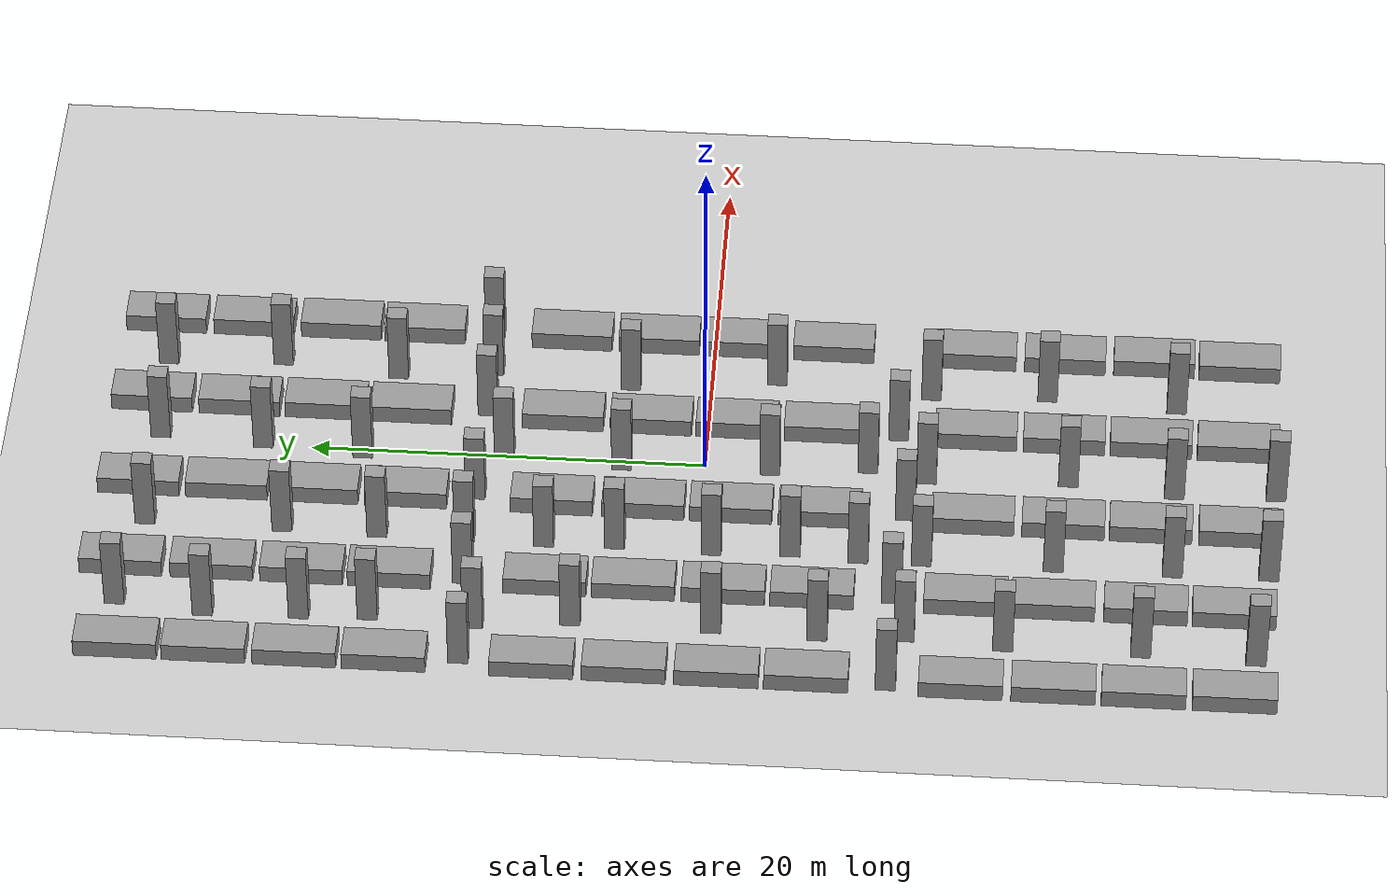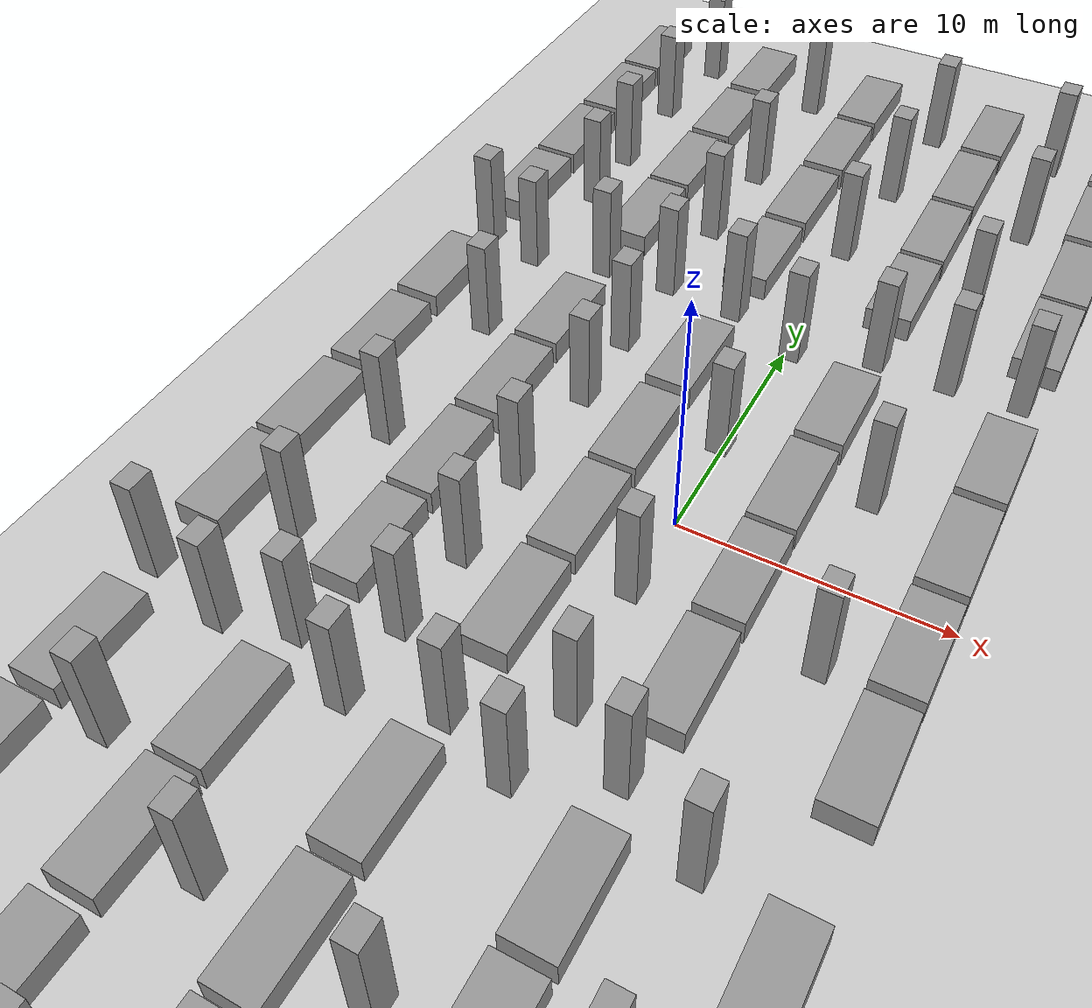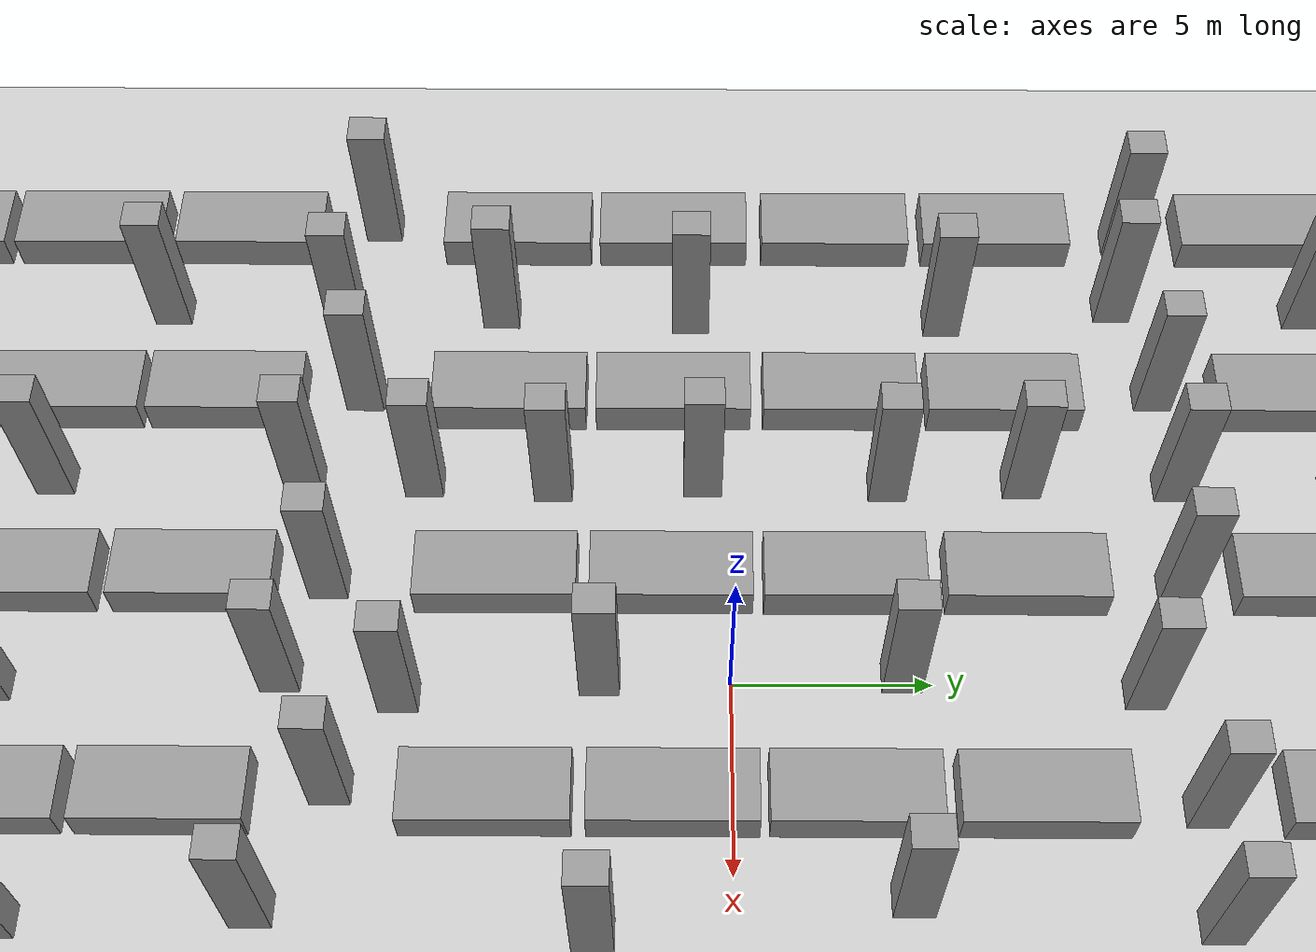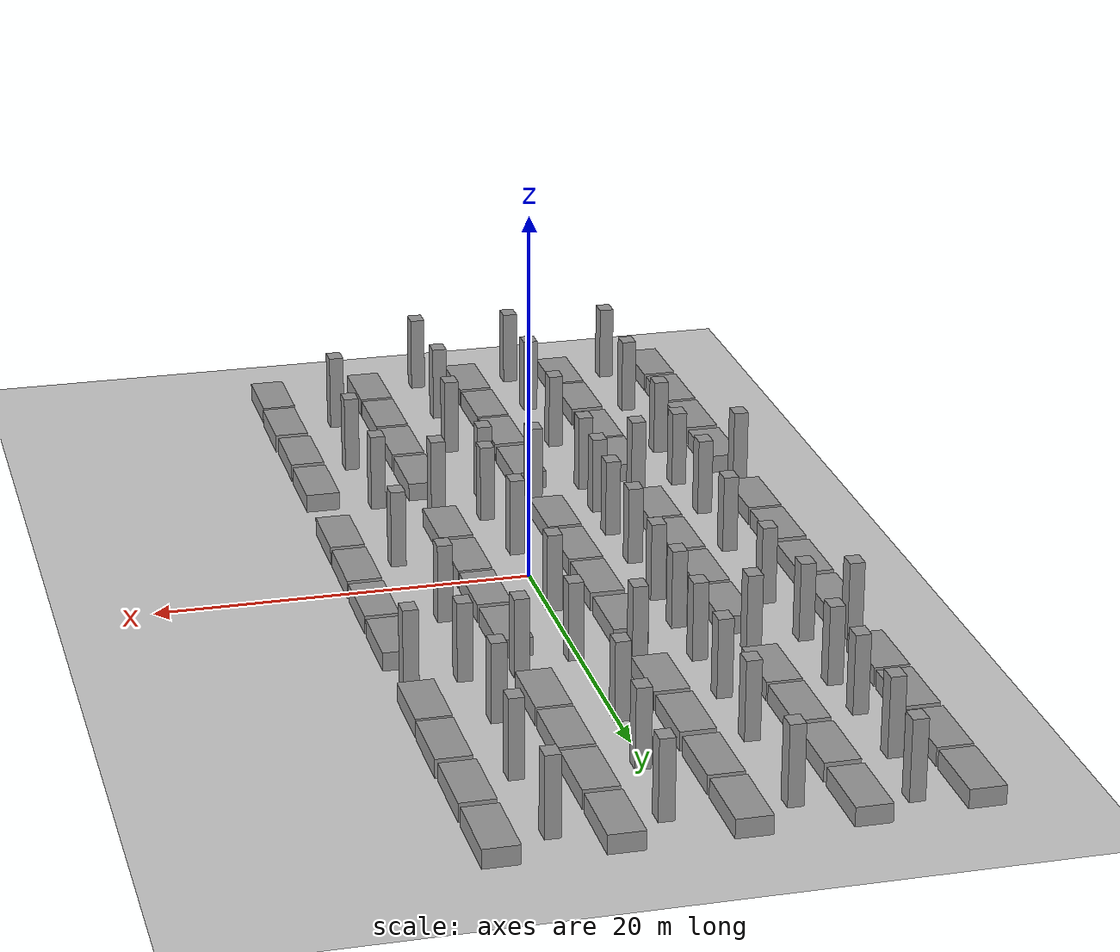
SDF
<sdf version="1.7">
 <world name="default">
  <light name="sun" type="directional">
   <pose>0 0 10 0 -0 0</pose>
   <diffuse>0.8 0.8 0.8 1</diffuse>
   <specular>0.2 0.2 0.2 1</specular>
   <attenuation>
    <range>1000</range>
    <constant>0.9</constant>
    <linear>0.01</linear>
    <quadratic>0.001</quadratic>
   </attenuation>
   <direction>-0.5 0.1 -0.9</direction>
   <spot><inner_angle>0</inner_angle><outer_angle>0</outer_angle><falloff>0</falloff></spot>
  </light>
  <model name="ground_plane">
   <static>1</static>
   <link name="link">
    <collision name="collision">
     <geometry><plane><normal>0 0 1</normal><size>100 100</size></plane></geometry>
     <surface>
      <contact><collide_bitmask>65535</collide_bitmask></contact>
      <friction><ode><mu>100</mu><mu2>50</mu2></ode></friction>
     </surface>
    </collision>
    <visual name="visual">
     <geometry><plane><normal>0 0 1</normal><size>100 100</size></plane></geometry>
     <material>
      <script><uri>file://media/materials/scripts/gazebo.material</uri><name>Gazebo/Grey</name></script>
     </material>
    </visual>
   </link>
  </model>
  <gravity>0 0 -9.8</gravity>
  <magnetic_field>6e-06 3e-05 -4.2e-05</magnetic_field>
  <atmosphere type="adiabatic"/>
  <physics type="ode">
   <max_step_size>0.001</max_step_size>
   <real_time_factor>1</real_time_factor>
   <real_time_update_rate>1000</real_time_update_rate>
  </physics>
  <scene><ambient>0.4 0.4 0.4 1</ambient><background>0.7 0.7 0.7 1</background><shadows>1</shadows></scene>
  <spherical_coordinates>
   <surface_model>EARTH_WGS84</surface_model>
   <latitude_deg>0</latitude_deg>
   <longitude_deg>0</longitude_deg>
   <elevation>0</elevation>
   <heading_deg>0</heading_deg>
  </spherical_coordinates>
  <model name="unit_box">
   <pose>8.90241 -26.8368 0.5 -0 1e-06 0.001252</pose>
   <link name="link">
    <inertial>
     <mass>1</mass>
     <inertia>
      <ixx>0.166667</ixx>
      <ixy>0</ixy>
      <ixz>0</ixz>
      <iyy>0.166667</iyy>
      <iyz>0</iyz>
      <izz>0.166667</izz>
     </inertia>
    </inertial>
    <collision name="collision"><geometry><box><size>1.85096 4.12993 1</size></box></geometry></collision>
    <visual name="visual">
     <geometry><box><size>1.85096 4.12993 1</size></box></geometry>
     <material>
      <script><name>Gazebo/Grey</name><uri>file://media/materials/scripts/gazebo.material</uri></script>
     </material>
    </visual>
   </link>
  </model>
  <model name="unit_box_clone">
   <pose>8.96485 -22.4699 0.499996 0 5e-06 -0.000225</pose>
   <link name="link">
    <inertial>
     <mass>1</mass>
     <inertia>
      <ixx>0.166667</ixx>
      <ixy>0</ixy>
      <ixz>0</ixz>
      <iyy>0.166667</iyy>
      <iyz>0</iyz>
      <izz>0.166667</izz>
     </inertia>
    </inertial>
    <collision name="collision"><geometry><box><size>1.85096 4.12993 1</size></box></geometry></collision>
    <visual name="visual">
     <geometry><box><size>1.85096 4.12993 1</size></box></geometry>
     <material>
      <script><name>Gazebo/Grey</name><uri>file://media/materials/scripts/gazebo.material</uri></script>
     </material>
    </visual>
   </link>
  </model>
  <model name="unit_box_clone_clone">
   <pose>8.89161 -17.9103 0.499996 0 5e-06 -0.000242</pose>
   <link name="link">
    <inertial>
     <mass>1</mass>
     <inertia>
      <ixx>0.166667</ixx>
      <ixy>0</ixy>
      <ixz>0</ixz>
      <iyy>0.166667</iyy>
      <iyz>0</iyz>
      <izz>0.166667</izz>
     </inertia>
    </inertial>
    <collision name="collision"><geometry><box><size>1.85096 4.12993 1</size></box></geometry></collision>
    <visual name="visual">
     <geometry><box><size>1.85096 4.12993 1</size></box></geometry>
     <material>
      <script><name>Gazebo/Grey</name><uri>file://media/materials/scripts/gazebo.material</uri></script>
     </material>
    </visual>
   </link>
  </model>
  <model name="unit_box_clone_clone_0">
   <pose>8.88995 -13.3499 0.499996 0 5e-06 -0.000396</pose>
   <link name="link">
    <inertial>
     <mass>1</mass>
     <inertia>
      <ixx>0.166667</ixx>
      <ixy>0</ixy>
      <ixz>0</ixz>
      <iyy>0.166667</iyy>
      <iyz>0</iyz>
      <izz>0.166667</izz>
     </inertia>
    </inertial>
    <collision name="collision"><geometry><box><size>1.85096 4.12993 1</size></box></geometry></collision>
    <visual name="visual">
     <geometry><box><size>1.85096 4.12993 1</size></box></geometry>
     <material>
      <script><name>Gazebo/Grey</name><uri>file://media/materials/scripts/gazebo.material</uri></script>
     </material>
    </visual>
   </link>
  </model>
  <model name="unit_box_clone_clone_1">
   <pose>8.98225 -6.04845 0.499996 0 5e-06 -0.000487</pose>
   <link name="link">
    <inertial>
     <mass>1</mass>
     <inertia>
      <ixx>0.166667</ixx>
      <ixy>0</ixy>
      <ixz>0</ixz>
      <iyy>0.166667</iyy>
      <iyz>0</iyz>
      <izz>0.166667</izz>
     </inertia>
    </inertial>
    <collision name="collision"><geometry><box><size>1.85096 4.12993 1</size></box></geometry></collision>
    <visual name="visual">
     <geometry><box><size>1.85096 4.12993 1</size></box></geometry>
     <material>
      <script><name>Gazebo/Grey</name><uri>file://media/materials/scripts/gazebo.material</uri></script>
     </material>
    </visual>
   </link>
  </model>
  <model name="unit_box_clone_clone_2">
   <pose>8.98237 2.93253 0.499996 0 -5e-06 -0.001041</pose>
   <link name="link">
    <inertial>
     <mass>1</mass>
     <inertia>
      <ixx>0.166667</ixx>
      <ixy>0</ixy>
      <ixz>0</ixz>
      <iyy>0.166667</iyy>
      <iyz>0</iyz>
      <izz>0.166667</izz>
     </inertia>
    </inertial>
    <collision name="collision"><geometry><box><size>1.85096 4.12993 1</size></box></geometry></collision>
    <visual name="visual">
     <geometry><box><size>1.85096 4.12993 1</size></box></geometry>
     <material>
      <script><name>Gazebo/Grey</name><uri>file://media/materials/scripts/gazebo.material</uri></script>
     </material>
    </visual>
   </link>
  </model>
  <model name="unit_box_clone_clone_3">
   <pose>8.98226 -1.54834 0.5 0 -1e-06 -0.000107</pose>
   <link name="link">
    <inertial>
     <mass>1</mass>
     <inertia>
      <ixx>0.166667</ixx>
      <ixy>0</ixy>
      <ixz>0</ixz>
      <iyy>0.166667</iyy>
      <iyz>0</iyz>
      <izz>0.166667</izz>
     </inertia>
    </inertial>
    <collision name="collision"><geometry><box><size>1.85096 4.12993 1</size></box></geometry></collision>
    <visual name="visual">
     <geometry><box><size>1.85096 4.12993 1</size></box></geometry>
     <material>
      <script><name>Gazebo/Grey</name><uri>file://media/materials/scripts/gazebo.material</uri></script>
     </material>
    </visual>
   </link>
  </model>
  <model name="unit_box_clone_clone_4">
   <pose>8.98224 7.41455 0.5 0 -1e-06 -0.001076</pose>
   <link name="link">
    <inertial>
     <mass>1</mass>
     <inertia>
      <ixx>0.166667</ixx>
      <ixy>0</ixy>
      <ixz>0</ixz>
      <iyy>0.166667</iyy>
      <iyz>0</iyz>
      <izz>0.166667</izz>
     </inertia>
    </inertial>
    <collision name="collision"><geometry><box><size>1.85096 4.12993 1</size></box></geometry></collision>
    <visual name="visual">
     <geometry><box><size>1.85096 4.12993 1</size></box></geometry>
     <material>
      <script><name>Gazebo/Grey</name><uri>file://media/materials/scripts/gazebo.material</uri></script>
     </material>
    </visual>
   </link>
  </model>
  <model name="unit_box_clone_clone_5">
   <pose>8.98222 15.0009 0.5 0 -1e-06 0.00136</pose>
   <link name="link">
    <inertial>
     <mass>1</mass>
     <inertia>
      <ixx>0.166667</ixx>
      <ixy>0</ixy>
      <ixz>0</ixz>
      <iyy>0.166667</iyy>
      <iyz>0</iyz>
      <izz>0.166667</izz>
     </inertia>
    </inertial>
    <collision name="collision"><geometry><box><size>1.85096 4.12993 1</size></box></geometry></collision>
    <visual name="visual">
     <geometry><box><size>1.85096 4.12993 1</size></box></geometry>
     <material>
      <script><name>Gazebo/Grey</name><uri>file://media/materials/scripts/gazebo.material</uri></script>
     </material>
    </visual>
   </link>
  </model>
  <model name="unit_box_clone_clone_6">
   <pose>8.99544 19.3324 0.5 0 1e-06 0.001075</pose>
   <link name="link">
    <inertial>
     <mass>1</mass>
     <inertia>
      <ixx>0.166667</ixx>
      <ixy>0</ixy>
      <ixz>0</ixz>
      <iyy>0.166667</iyy>
      <iyz>0</iyz>
      <izz>0.166667</izz>
     </inertia>
    </inertial>
    <collision name="collision"><geometry><box><size>1.85096 4.12993 1</size></box></geometry></collision>
    <visual name="visual">
     <geometry><box><size>1.85096 4.12993 1</size></box></geometry>
     <material>
      <script><name>Gazebo/Grey</name><uri>file://media/materials/scripts/gazebo.material</uri></script>
     </material>
    </visual>
   </link>
  </model>
  <model name="unit_box_clone_clone_7">
   <pose>8.9102 23.8406 0.5 -0 -1e-06 0.0022</pose>
   <link name="link">
    <inertial>
     <mass>1</mass>
     <inertia>
      <ixx>0.166667</ixx>
      <ixy>0</ixy>
      <ixz>0</ixz>
      <iyy>0.166667</iyy>
      <iyz>0</iyz>
      <izz>0.166667</izz>
     </inertia>
    </inertial>
    <collision name="collision"><geometry><box><size>1.85096 4.12993 1</size></box></geometry></collision>
    <visual name="visual">
     <geometry><box><size>1.85096 4.12993 1</size></box></geometry>
     <material>
      <script><name>Gazebo/Grey</name><uri>file://media/materials/scripts/gazebo.material</uri></script>
     </material>
    </visual>
   </link>
  </model>
  <model name="unit_box_clone_clone_8">
   <pose>8.89401 28.3719 0.5 0 -1e-06 0.002603</pose>
   <link name="link">
    <inertial>
     <mass>1</mass>
     <inertia>
      <ixx>0.166667</ixx>
      <ixy>0</ixy>
      <ixz>0</ixz>
      <iyy>0.166667</iyy>
      <iyz>0</iyz>
      <izz>0.166667</izz>
     </inertia>
    </inertial>
    <collision name="collision"><geometry><box><size>1.85096 4.12993 1</size></box></geometry></collision>
    <visual name="visual">
     <geometry><box><size>1.85096 4.12993 1</size></box></geometry>
     <material>
      <script><name>Gazebo/Grey</name><uri>file://media/materials/scripts/gazebo.material</uri></script>
     </material>
    </visual>
   </link>
  </model>
  <model name="unit_box_clone_clone_10">
   <pose>3.08007 23.9434 0.5 0 1e-06 0.001733</pose>
   <link name="link">
    <inertial>
     <mass>1</mass>
     <inertia>
      <ixx>0.166667</ixx>
      <ixy>0</ixy>
      <ixz>0</ixz>
      <iyy>0.166667</iyy>
      <iyz>0</iyz>
      <izz>0.166667</izz>
     </inertia>
    </inertial>
    <collision name="collision"><geometry><box><size>1.85096 4.12993 1</size></box></geometry></collision>
    <visual name="visual">
     <geometry><box><size>1.85096 4.12993 1</size></box></geometry>
     <material>
      <script><name>Gazebo/Grey</name><uri>file://media/materials/scripts/gazebo.material</uri></script>
     </material>
    </visual>
   </link>
  </model>
  <model name="unit_box_clone_clone_11">
   <pose>3.08879 19.533 0.5 0 1e-06 -0.001462</pose>
   <link name="link">
    <inertial>
     <mass>1</mass>
     <inertia>
      <ixx>0.166667</ixx>
      <ixy>0</ixy>
      <ixz>0</ixz>
      <iyy>0.166667</iyy>
      <iyz>0</iyz>
      <izz>0.166667</izz>
     </inertia>
    </inertial>
    <collision name="collision"><geometry><box><size>1.85096 4.12993 1</size></box></geometry></collision>
    <visual name="visual">
     <geometry><box><size>1.85096 4.12993 1</size></box></geometry>
     <material>
      <script><name>Gazebo/Grey</name><uri>file://media/materials/scripts/gazebo.material</uri></script>
     </material>
    </visual>
   </link>
  </model>
  <model name="unit_box_clone_clone_12">
   <pose>3.07998 15.1593 0.499996 0 5e-06 0.000403</pose>
   <link name="link">
    <inertial>
     <mass>1</mass>
     <inertia>
      <ixx>0.166667</ixx>
      <ixy>0</ixy>
      <ixz>0</ixz>
      <iyy>0.166667</iyy>
      <iyz>0</iyz>
      <izz>0.166667</izz>
     </inertia>
    </inertial>
    <collision name="collision"><geometry><box><size>1.85096 4.12993 1</size></box></geometry></collision>
    <visual name="visual">
     <geometry><box><size>1.85096 4.12993 1</size></box></geometry>
     <material>
      <script><name>Gazebo/Grey</name><uri>file://media/materials/scripts/gazebo.material</uri></script>
     </material>
    </visual>
   </link>
  </model>
  <model name="unit_box_clone_clone_13">
   <pose>3.0803 7.42133 0.499996 0 -5e-06 0.000162</pose>
   <link name="link">
    <inertial>
     <mass>1</mass>
     <inertia>
      <ixx>0.166667</ixx>
      <ixy>0</ixy>
      <ixz>0</ixz>
      <iyy>0.166667</iyy>
      <iyz>0</iyz>
      <izz>0.166667</izz>
     </inertia>
    </inertial>
    <collision name="collision"><geometry><box><size>1.85096 4.12993 1</size></box></geometry></collision>
    <visual name="visual">
     <geometry><box><size>1.85096 4.12993 1</size></box></geometry>
     <material>
      <script><name>Gazebo/Grey</name><uri>file://media/materials/scripts/gazebo.material</uri></script>
     </material>
    </visual>
   </link>
  </model>
  <model name="unit_box_clone_clone_14">
   <pose>3.0803 2.93003 0.5 0 -1e-06 -0.000976</pose>
   <link name="link">
    <inertial>
     <mass>1</mass>
     <inertia>
      <ixx>0.166667</ixx>
      <ixy>0</ixy>
      <ixz>0</ixz>
      <iyy>0.166667</iyy>
      <iyz>0</iyz>
      <izz>0.166667</izz>
     </inertia>
    </inertial>
    <collision name="collision"><geometry><box><size>1.85096 4.12993 1</size></box></geometry></collision>
    <visual name="visual">
     <geometry><box><size>1.85096 4.12993 1</size></box></geometry>
     <material>
      <script><name>Gazebo/Grey</name><uri>file://media/materials/scripts/gazebo.material</uri></script>
     </material>
    </visual>
   </link>
  </model>
  <model name="unit_box_clone_clone_15">
   <pose>3.08121 -1.42818 0.5 -0 -1e-06 -0.001181</pose>
   <link name="link">
    <inertial>
     <mass>1</mass>
     <inertia>
      <ixx>0.166667</ixx>
      <ixy>0</ixy>
      <ixz>0</ixz>
      <iyy>0.166667</iyy>
      <iyz>0</iyz>
      <izz>0.166667</izz>
     </inertia>
    </inertial>
    <collision name="collision"><geometry><box><size>1.85096 4.12993 1</size></box></geometry></collision>
    <visual name="visual">
     <geometry><box><size>1.85096 4.12993 1</size></box></geometry>
     <material>
      <script><name>Gazebo/Grey</name><uri>file://media/materials/scripts/gazebo.material</uri></script>
     </material>
    </visual>
   </link>
  </model>
  <model name="unit_box_clone_clone_16">
   <pose>3.08031 -5.90701 0.5 -0 1e-06 0.000942</pose>
   <link name="link">
    <inertial>
     <mass>1</mass>
     <inertia>
      <ixx>0.166667</ixx>
      <ixy>0</ixy>
      <ixz>0</ixz>
      <iyy>0.166667</iyy>
      <iyz>0</iyz>
      <izz>0.166667</izz>
     </inertia>
    </inertial>
    <collision name="collision"><geometry><box><size>1.85096 4.12993 1</size></box></geometry></collision>
    <visual name="visual">
     <geometry><box><size>1.85096 4.12993 1</size></box></geometry>
     <material>
      <script><name>Gazebo/Grey</name><uri>file://media/materials/scripts/gazebo.material</uri></script>
     </material>
    </visual>
   </link>
  </model>
  <model name="unit_box_clone_clone_17">
   <pose>3.08032 -13.5734 0.5 -0 -1e-06 -0.001711</pose>
   <link name="link">
    <inertial>
     <mass>1</mass>
     <inertia>
      <ixx>0.166667</ixx>
      <ixy>0</ixy>
      <ixz>0</ixz>
      <iyy>0.166667</iyy>
      <iyz>0</iyz>
      <izz>0.166667</izz>
     </inertia>
    </inertial>
    <collision name="collision"><geometry><box><size>1.85096 4.12993 1</size></box></geometry></collision>
    <visual name="visual">
     <geometry><box><size>1.85096 4.12993 1</size></box></geometry>
     <material>
      <script><name>Gazebo/Grey</name><uri>file://media/materials/scripts/gazebo.material</uri></script>
     </material>
    </visual>
   </link>
  </model>
  <model name="unit_box_clone_clone_18">
   <pose>3.08001 -18.0322 0.5 -0 1e-06 0.002271</pose>
   <link name="link">
    <inertial>
     <mass>1</mass>
     <inertia>
      <ixx>0.166667</ixx>
      <ixy>0</ixy>
      <ixz>0</ixz>
      <iyy>0.166667</iyy>
      <iyz>0</iyz>
      <izz>0.166667</izz>
     </inertia>
    </inertial>
    <collision name="collision"><geometry><box><size>1.85096 4.12993 1</size></box></geometry></collision>
    <visual name="visual">
     <geometry><box><size>1.85096 4.12993 1</size></box></geometry>
     <material>
      <script><name>Gazebo/Grey</name><uri>file://media/materials/scripts/gazebo.material</uri></script>
     </material>
    </visual>
   </link>
  </model>
  <model name="unit_box_clone_clone_19">
   <pose>3.08438 -22.4365 0.499996 0 -5e-06 0.000502</pose>
   <link name="link">
    <inertial>
     <mass>1</mass>
     <inertia>
      <ixx>0.166667</ixx>
      <ixy>0</ixy>
      <ixz>0</ixz>
      <iyy>0.166667</iyy>
      <iyz>0</iyz>
      <izz>0.166667</izz>
     </inertia>
    </inertial>
    <collision name="collision"><geometry><box><size>1.85096 4.12993 1</size></box></geometry></collision>
    <visual name="visual">
     <geometry><box><size>1.85096 4.12993 1</size></box></geometry>
     <material>
      <script><name>Gazebo/Grey</name><uri>file://media/materials/scripts/gazebo.material</uri></script>
     </material>
    </visual>
   </link>
  </model>
  <model name="unit_box_clone_clone_20">
   <pose>3.08835 -26.8512 0.5 0 -1e-06 0.001174</pose>
   <link name="link">
    <inertial>
     <mass>1</mass>
     <inertia>
      <ixx>0.166667</ixx>
      <ixy>0</ixy>
      <ixz>0</ixz>
      <iyy>0.166667</iyy>
      <iyz>0</iyz>
      <izz>0.166667</izz>
     </inertia>
    </inertial>
    <collision name="collision"><geometry><box><size>1.85096 4.12993 1</size></box></geometry></collision>
    <visual name="visual">
     <geometry><box><size>1.85096 4.12993 1</size></box></geometry>
     <material>
      <script><name>Gazebo/Grey</name><uri>file://media/materials/scripts/gazebo.material</uri></script>
     </material>
    </visual>
   </link>
  </model>
  <model name="unit_box_clone_clone_21">
   <pose>-2.93399 -27.0156 0.499996 0 5e-06 -0.000369</pose>
   <link name="link">
    <inertial>
     <mass>1</mass>
     <inertia>
      <ixx>0.166667</ixx>
      <ixy>0</ixy>
      <ixz>0</ixz>
      <iyy>0.166667</iyy>
      <iyz>0</iyz>
      <izz>0.166667</izz>
     </inertia>
    </inertial>
    <collision name="collision"><geometry><box><size>1.85096 4.12993 1</size></box></geometry></collision>
    <visual name="visual">
     <geometry><box><size>1.85096 4.12993 1</size></box></geometry>
     <material>
      <script><name>Gazebo/Grey</name><uri>file://media/materials/scripts/gazebo.material</uri></script>
     </material>
    </visual>
   </link>
  </model>
  <model name="unit_box_clone_clone_22">
   <pose>-2.93399 -22.5461 0.499996 -0 -5e-06 0.000186</pose>
   <link name="link">
    <inertial>
     <mass>1</mass>
     <inertia>
      <ixx>0.166667</ixx>
      <ixy>0</ixy>
      <ixz>0</ixz>
      <iyy>0.166667</iyy>
      <iyz>0</iyz>
      <izz>0.166667</izz>
     </inertia>
    </inertial>
    <collision name="collision"><geometry><box><size>1.85096 4.12993 1</size></box></geometry></collision>
    <visual name="visual">
     <geometry><box><size>1.85096 4.12993 1</size></box></geometry>
     <material>
      <script><name>Gazebo/Grey</name><uri>file://media/materials/scripts/gazebo.material</uri></script>
     </material>
    </visual>
   </link>
  </model>
  <model name="unit_box_clone_clone_23">
   <pose>-2.93399 -18.1654 0.499996 0 -5e-06 -1.9e-05</pose>
   <link name="link">
    <inertial>
     <mass>1</mass>
     <inertia>
      <ixx>0.166667</ixx>
      <ixy>0</ixy>
      <ixz>0</ixz>
      <iyy>0.166667</iyy>
      <iyz>0</iyz>
      <izz>0.166667</izz>
     </inertia>
    </inertial>
    <collision name="collision"><geometry><box><size>1.85096 4.12993 1</size></box></geometry></collision>
    <visual name="visual">
     <geometry><box><size>1.85096 4.12993 1</size></box></geometry>
     <material>
      <script><name>Gazebo/Grey</name><uri>file://media/materials/scripts/gazebo.material</uri></script>
     </material>
    </visual>
   </link>
  </model>
  <model name="unit_box_clone_clone_24">
   <pose>-2.934 -13.6376 0.5 0 -1e-06 -0.001213</pose>
   <link name="link">
    <inertial>
     <mass>1</mass>
     <inertia>
      <ixx>0.166667</ixx>
      <ixy>0</ixy>
      <ixz>0</ixz>
      <iyy>0.166667</iyy>
      <iyz>0</iyz>
      <izz>0.166667</izz>
     </inertia>
    </inertial>
    <collision name="collision"><geometry><box><size>1.85096 4.12993 1</size></box></geometry></collision>
    <visual name="visual">
     <geometry><box><size>1.85096 4.12993 1</size></box></geometry>
     <material>
      <script><name>Gazebo/Grey</name><uri>file://media/materials/scripts/gazebo.material</uri></script>
     </material>
    </visual>
   </link>
  </model>
  <model name="unit_box_clone_clone_25">
   <pose>-2.93405 -5.96208 0.5 0 -1e-06 0.00233</pose>
   <link name="link">
    <inertial>
     <mass>1</mass>
     <inertia>
      <ixx>0.166667</ixx>
      <ixy>0</ixy>
      <ixz>0</ixz>
      <iyy>0.166667</iyy>
      <iyz>0</iyz>
      <izz>0.166667</izz>
     </inertia>
    </inertial>
    <collision name="collision"><geometry><box><size>1.85096 4.12993 1</size></box></geometry></collision>
    <visual name="visual">
     <geometry><box><size>1.85096 4.12993 1</size></box></geometry>
     <material>
      <script><name>Gazebo/Grey</name><uri>file://media/materials/scripts/gazebo.material</uri></script>
     </material>
    </visual>
   </link>
  </model>
  <model name="unit_box_clone_clone_26">
   <pose>-2.934 -1.5017 0.5 0 -1e-06 0.001041</pose>
   <link name="link">
    <inertial>
     <mass>1</mass>
     <inertia>
      <ixx>0.166667</ixx>
      <ixy>0</ixy>
      <ixz>0</ixz>
      <iyy>0.166667</iyy>
      <iyz>0</iyz>
      <izz>0.166667</izz>
     </inertia>
    </inertial>
    <collision name="collision"><geometry><box><size>1.85096 4.12993 1</size></box></geometry></collision>
    <visual name="visual">
     <geometry><box><size>1.85096 4.12993 1</size></box></geometry>
     <material>
      <script><name>Gazebo/Grey</name><uri>file://media/materials/scripts/gazebo.material</uri></script>
     </material>
    </visual>
   </link>
  </model>
  <model name="unit_box_clone_clone_27">
   <pose>-2.934 2.90946 0.5 0 1e-06 0.001432</pose>
   <link name="link">
    <inertial>
     <mass>1</mass>
     <inertia>
      <ixx>0.166667</ixx>
      <ixy>0</ixy>
      <ixz>0</ixz>
      <iyy>0.166667</iyy>
      <iyz>0</iyz>
      <izz>0.166667</izz>
     </inertia>
    </inertial>
    <collision name="collision"><geometry><box><size>1.85096 4.12993 1</size></box></geometry></collision>
    <visual name="visual">
     <geometry><box><size>1.85096 4.12993 1</size></box></geometry>
     <material>
      <script><name>Gazebo/Grey</name><uri>file://media/materials/scripts/gazebo.material</uri></script>
     </material>
    </visual>
   </link>
  </model>
  <model name="unit_box_clone_clone_28">
   <pose>-2.93399 7.51229 0.5 -0 -1e-06 -0.005582</pose>
   <link name="link">
    <inertial>
     <mass>1</mass>
     <inertia>
      <ixx>0.166667</ixx>
      <ixy>0</ixy>
      <ixz>0</ixz>
      <iyy>0.166667</iyy>
      <iyz>0</iyz>
      <izz>0.166667</izz>
     </inertia>
    </inertial>
    <collision name="collision"><geometry><box><size>1.85096 4.12993 1</size></box></geometry></collision>
    <visual name="visual">
     <geometry><box><size>1.85096 4.12993 1</size></box></geometry>
     <material>
      <script><name>Gazebo/Grey</name><uri>file://media/materials/scripts/gazebo.material</uri></script>
     </material>
    </visual>
   </link>
  </model>
  <model name="unit_box_clone_clone_29">
   <pose>-2.93397 14.8688 0.499996 0 -5e-06 0.000452</pose>
   <link name="link">
    <inertial>
     <mass>1</mass>
     <inertia>
      <ixx>0.166667</ixx>
      <ixy>0</ixy>
      <ixz>0</ixz>
      <iyy>0.166667</iyy>
      <iyz>0</iyz>
      <izz>0.166667</izz>
     </inertia>
    </inertial>
    <collision name="collision"><geometry><box><size>1.85096 4.12993 1</size></box></geometry></collision>
    <visual name="visual">
     <geometry><box><size>1.85096 4.12993 1</size></box></geometry>
     <material>
      <script><name>Gazebo/Grey</name><uri>file://media/materials/scripts/gazebo.material</uri></script>
     </material>
    </visual>
   </link>
  </model>
  <model name="unit_box_clone_clone_30">
   <pose>-2.93397 19.3398 0.499996 0 5e-06 -0.000549</pose>
   <link name="link">
    <inertial>
     <mass>1</mass>
     <inertia>
      <ixx>0.166667</ixx>
      <ixy>0</ixy>
      <ixz>0</ixz>
      <iyy>0.166667</iyy>
      <iyz>0</iyz>
      <izz>0.166667</izz>
     </inertia>
    </inertial>
    <collision name="collision"><geometry><box><size>1.85096 4.12993 1</size></box></geometry></collision>
    <visual name="visual">
     <geometry><box><size>1.85096 4.12993 1</size></box></geometry>
     <material>
      <script><name>Gazebo/Grey</name><uri>file://media/materials/scripts/gazebo.material</uri></script>
     </material>
    </visual>
   </link>
  </model>
  <model name="unit_box_clone_clone_31">
   <pose>-2.93402 23.9223 0.5 0 1e-06 0.001463</pose>
   <link name="link">
    <inertial>
     <mass>1</mass>
     <inertia>
      <ixx>0.166667</ixx>
      <ixy>0</ixy>
      <ixz>0</ixz>
      <iyy>0.166667</iyy>
      <iyz>0</iyz>
      <izz>0.166667</izz>
     </inertia>
    </inertial>
    <collision name="collision"><geometry><box><size>1.85096 4.12993 1</size></box></geometry></collision>
    <visual name="visual">
     <geometry><box><size>1.85096 4.12993 1</size></box></geometry>
     <material>
      <script><name>Gazebo/Grey</name><uri>file://media/materials/scripts/gazebo.material</uri></script>
     </material>
    </visual>
   </link>
  </model>
  <model name="unit_box_clone_clone_32">
   <pose>-2.93451 28.3743 0.5 0 -1e-06 -0.00363</pose>
   <link name="link">
    <inertial>
     <mass>1</mass>
     <inertia>
      <ixx>0.166667</ixx>
      <ixy>0</ixy>
      <ixz>0</ixz>
      <iyy>0.166667</iyy>
      <iyz>0</iyz>
      <izz>0.166667</izz>
     </inertia>
    </inertial>
    <collision name="collision"><geometry><box><size>1.85096 4.12993 1</size></box></geometry></collision>
    <visual name="visual">
     <geometry><box><size>1.85096 4.12993 1</size></box></geometry>
     <material>
      <script><name>Gazebo/Grey</name><uri>file://media/materials/scripts/gazebo.material</uri></script>
     </material>
    </visual>
   </link>
  </model>
  <model name="unit_box_clone_clone_33">
   <pose>-8.57999 -26.7871 0.499996 0 5e-06 0.000206</pose>
   <link name="link">
    <inertial>
     <mass>1</mass>
     <inertia>
      <ixx>0.166667</ixx>
      <ixy>0</ixy>
      <ixz>0</ixz>
      <iyy>0.166667</iyy>
      <iyz>0</iyz>
      <izz>0.166667</izz>
     </inertia>
    </inertial>
    <collision name="collision"><geometry><box><size>1.85096 4.12993 1</size></box></geometry></collision>
    <visual name="visual">
     <geometry><box><size>1.85096 4.12993 1</size></box></geometry>
     <material>
      <script><name>Gazebo/Grey</name><uri>file://media/materials/scripts/gazebo.material</uri></script>
     </material>
    </visual>
   </link>
  </model>
  <model name="unit_box_clone_clone_34">
   <pose>-8.58 -22.4107 0.5 0 1e-06 -0.000679</pose>
   <link name="link">
    <inertial>
     <mass>1</mass>
     <inertia>
      <ixx>0.166667</ixx>
      <ixy>0</ixy>
      <ixz>0</ixz>
      <iyy>0.166667</iyy>
      <iyz>0</iyz>
      <izz>0.166667</izz>
     </inertia>
    </inertial>
    <collision name="collision"><geometry><box><size>1.85096 4.12993 1</size></box></geometry></collision>
    <visual name="visual">
     <geometry><box><size>1.85096 4.12993 1</size></box></geometry>
     <material>
      <script><name>Gazebo/Grey</name><uri>file://media/materials/scripts/gazebo.material</uri></script>
     </material>
    </visual>
   </link>
  </model>
  <model name="unit_box_clone_clone_35">
   <pose>-8.58001 -17.828 0.5 -0 -1e-06 0.000929</pose>
   <link name="link">
    <inertial>
     <mass>1</mass>
     <inertia>
      <ixx>0.166667</ixx>
      <ixy>0</ixy>
      <ixz>0</ixz>
      <iyy>0.166667</iyy>
      <iyz>0</iyz>
      <izz>0.166667</izz>
     </inertia>
    </inertial>
    <collision name="collision"><geometry><box><size>1.85096 4.12993 1</size></box></geometry></collision>
    <visual name="visual">
     <geometry><box><size>1.85096 4.12993 1</size></box></geometry>
     <material>
      <script><name>Gazebo/Grey</name><uri>file://media/materials/scripts/gazebo.material</uri></script>
     </material>
    </visual>
   </link>
  </model>
  <model name="unit_box_clone_clone_36">
   <pose>-8.58 -13.4881 0.5 -0 1e-06 -0.000877</pose>
   <link name="link">
    <inertial>
     <mass>1</mass>
     <inertia>
      <ixx>0.166667</ixx>
      <ixy>0</ixy>
      <ixz>0</ixz>
      <iyy>0.166667</iyy>
      <iyz>0</iyz>
      <izz>0.166667</izz>
     </inertia>
    </inertial>
    <collision name="collision"><geometry><box><size>1.85096 4.12993 1</size></box></geometry></collision>
    <visual name="visual">
     <geometry><box><size>1.85096 4.12993 1</size></box></geometry>
     <material>
      <script><name>Gazebo/Grey</name><uri>file://media/materials/scripts/gazebo.material</uri></script>
     </material>
    </visual>
   </link>
  </model>
  <model name="unit_box_clone_clone_37">
   <pose>-8.57999 -5.87789 0.499996 0 5e-06 -0.001114</pose>
   <link name="link">
    <inertial>
     <mass>1</mass>
     <inertia>
      <ixx>0.166667</ixx>
      <ixy>0</ixy>
      <ixz>0</ixz>
      <iyy>0.166667</iyy>
      <iyz>0</iyz>
      <izz>0.166667</izz>
     </inertia>
    </inertial>
    <collision name="collision"><geometry><box><size>1.85096 4.12993 1</size></box></geometry></collision>
    <visual name="visual">
     <geometry><box><size>1.85096 4.12993 1</size></box></geometry>
     <material>
      <script><name>Gazebo/Grey</name><uri>file://media/materials/scripts/gazebo.material</uri></script>
     </material>
    </visual>
   </link>
  </model>
  <model name="unit_box_clone_clone_38">
   <pose>-8.58001 -1.47265 0.499996 0 5e-06 0.000312</pose>
   <link name="link">
    <inertial>
     <mass>1</mass>
     <inertia>
      <ixx>0.166667</ixx>
      <ixy>0</ixy>
      <ixz>0</ixz>
      <iyy>0.166667</iyy>
      <iyz>0</iyz>
      <izz>0.166667</izz>
     </inertia>
    </inertial>
    <collision name="collision"><geometry><box><size>1.85096 4.12993 1</size></box></geometry></collision>
    <visual name="visual">
     <geometry><box><size>1.85096 4.12993 1</size></box></geometry>
     <material>
      <script><name>Gazebo/Grey</name><uri>file://media/materials/scripts/gazebo.material</uri></script>
     </material>
    </visual>
   </link>
  </model>
  <model name="unit_box_clone_clone_39">
   <pose>-8.58 3.00347 0.499996 0 5e-06 0.000267</pose>
   <link name="link">
    <inertial>
     <mass>1</mass>
     <inertia>
      <ixx>0.166667</ixx>
      <ixy>0</ixy>
      <ixz>0</ixz>
      <iyy>0.166667</iyy>
      <iyz>0</iyz>
      <izz>0.166667</izz>
     </inertia>
    </inertial>
    <collision name="collision"><geometry><box><size>1.85096 4.12993 1</size></box></geometry></collision>
    <visual name="visual">
     <geometry><box><size>1.85096 4.12993 1</size></box></geometry>
     <material>
      <script><name>Gazebo/Grey</name><uri>file://media/materials/scripts/gazebo.material</uri></script>
     </material>
    </visual>
   </link>
  </model>
  <model name="unit_box_clone_clone_40">
   <pose>-8.57999 7.40229 0.5 0 -1e-06 -0.000532</pose>
   <link name="link">
    <inertial>
     <mass>1</mass>
     <inertia>
      <ixx>0.166667</ixx>
      <ixy>0</ixy>
      <ixz>0</ixz>
      <iyy>0.166667</iyy>
      <iyz>0</iyz>
      <izz>0.166667</izz>
     </inertia>
    </inertial>
    <collision name="collision"><geometry><box><size>1.85096 4.12993 1</size></box></geometry></collision>
    <visual name="visual">
     <geometry><box><size>1.85096 4.12993 1</size></box></geometry>
     <material>
      <script><name>Gazebo/Grey</name><uri>file://media/materials/scripts/gazebo.material</uri></script>
     </material>
    </visual>
   </link>
  </model>
  <model name="unit_box_clone_clone_41">
   <pose>-8.58 15.161 0.499996 0 -5e-06 0.000305</pose>
   <link name="link">
    <inertial>
     <mass>1</mass>
     <inertia>
      <ixx>0.166667</ixx>
      <ixy>0</ixy>
      <ixz>0</ixz>
      <iyy>0.166667</iyy>
      <iyz>0</iyz>
      <izz>0.166667</izz>
     </inertia>
    </inertial>
    <collision name="collision"><geometry><box><size>1.85096 4.12993 1</size></box></geometry></collision>
    <visual name="visual">
     <geometry><box><size>1.85096 4.12993 1</size></box></geometry>
     <material>
      <script><name>Gazebo/Grey</name><uri>file://media/materials/scripts/gazebo.material</uri></script>
     </material>
    </visual>
   </link>
  </model>
  <model name="unit_box_clone_clone_42">
   <pose>-8.57999 19.5393 0.5 0 1e-06 -0.001511</pose>
   <link name="link">
    <inertial>
     <mass>1</mass>
     <inertia>
      <ixx>0.166667</ixx>
      <ixy>0</ixy>
      <ixz>0</ixz>
      <iyy>0.166667</iyy>
      <iyz>0</iyz>
      <izz>0.166667</izz>
     </inertia>
    </inertial>
    <collision name="collision"><geometry><box><size>1.85096 4.12993 1</size></box></geometry></collision>
    <visual name="visual">
     <geometry><box><size>1.85096 4.12993 1</size></box></geometry>
     <material>
      <script><name>Gazebo/Grey</name><uri>file://media/materials/scripts/gazebo.material</uri></script>
     </material>
    </visual>
   </link>
  </model>
  <model name="unit_box_clone_clone_43">
   <pose>-8.58 24.0344 0.499996 -0 5e-06 -0.000174</pose>
   <link name="link">
    <inertial>
     <mass>1</mass>
     <inertia>
      <ixx>0.166667</ixx>
      <ixy>0</ixy>
      <ixz>0</ixz>
      <iyy>0.166667</iyy>
      <iyz>0</iyz>
      <izz>0.166667</izz>
     </inertia>
    </inertial>
    <collision name="collision"><geometry><box><size>1.85096 4.12993 1</size></box></geometry></collision>
    <visual name="visual">
     <geometry><box><size>1.85096 4.12993 1</size></box></geometry>
     <material>
      <script><name>Gazebo/Grey</name><uri>file://media/materials/scripts/gazebo.material</uri></script>
     </material>
    </visual>
   </link>
  </model>
  <model name="unit_box_clone_clone_44">
   <pose>-8.57963 28.5864 0.5 0 1e-06 0.000832</pose>
   <link name="link">
    <inertial>
     <mass>1</mass>
     <inertia>
      <ixx>0.166667</ixx>
      <ixy>0</ixy>
      <ixz>0</ixz>
      <iyy>0.166667</iyy>
      <iyz>0</iyz>
      <izz>0.166667</izz>
     </inertia>
    </inertial>
    <collision name="collision"><geometry><box><size>1.85096 4.12993 1</size></box></geometry></collision>
    <visual name="visual">
     <geometry><box><size>1.85096 4.12993 1</size></box></geometry>
     <material>
      <script><name>Gazebo/Grey</name><uri>file://media/materials/scripts/gazebo.material</uri></script>
     </material>
    </visual>
   </link>
  </model>
  <model name="unit_box_clone_clone_45">
   <pose>-14.24 28.1685 0.499996 0 5e-06 0.001657</pose>
   <link name="link">
    <inertial>
     <mass>1</mass>
     <inertia>
      <ixx>0.166667</ixx>
      <ixy>0</ixy>
      <ixz>0</ixz>
      <iyy>0.166667</iyy>
      <iyz>0</iyz>
      <izz>0.166667</izz>
     </inertia>
    </inertial>
    <collision name="collision"><geometry><box><size>1.85096 4.12993 1</size></box></geometry></collision>
    <visual name="visual">
     <geometry><box><size>1.85096 4.12993 1</size></box></geometry>
     <material>
      <script><name>Gazebo/Grey</name><uri>file://media/materials/scripts/gazebo.material</uri></script>
     </material>
    </visual>
   </link>
  </model>
  <model name="unit_box_clone_clone_46">
   <pose>-14.24 23.7872 0.499996 0 5e-06 0.000206</pose>
   <link name="link">
    <inertial>
     <mass>1</mass>
     <inertia>
      <ixx>0.166667</ixx>
      <ixy>0</ixy>
      <ixz>0</ixz>
      <iyy>0.166667</iyy>
      <iyz>0</iyz>
      <izz>0.166667</izz>
     </inertia>
    </inertial>
    <collision name="collision"><geometry><box><size>1.85096 4.12993 1</size></box></geometry></collision>
    <visual name="visual">
     <geometry><box><size>1.85096 4.12993 1</size></box></geometry>
     <material>
      <script><name>Gazebo/Grey</name><uri>file://media/materials/scripts/gazebo.material</uri></script>
     </material>
    </visual>
   </link>
  </model>
  <model name="unit_box_clone_clone_47">
   <pose>-14.24 19.2992 0.499996 -0 -5e-06 1.6e-05</pose>
   <link name="link">
    <inertial>
     <mass>1</mass>
     <inertia>
      <ixx>0.166667</ixx>
      <ixy>0</ixy>
      <ixz>0</ixz>
      <iyy>0.166667</iyy>
      <iyz>0</iyz>
      <izz>0.166667</izz>
     </inertia>
    </inertial>
    <collision name="collision"><geometry><box><size>1.85096 4.12993 1</size></box></geometry></collision>
    <visual name="visual">
     <geometry><box><size>1.85096 4.12993 1</size></box></geometry>
     <material>
      <script><name>Gazebo/Grey</name><uri>file://media/materials/scripts/gazebo.material</uri></script>
     </material>
    </visual>
   </link>
  </model>
  <model name="unit_box_clone_clone_48">
   <pose>-14.24 14.8894 0.5 -0 -1e-06 0.00137</pose>
   <link name="link">
    <inertial>
     <mass>1</mass>
     <inertia>
      <ixx>0.166667</ixx>
      <ixy>0</ixy>
      <ixz>0</ixz>
      <iyy>0.166667</iyy>
      <iyz>0</iyz>
      <izz>0.166667</izz>
     </inertia>
    </inertial>
    <collision name="collision"><geometry><box><size>1.85096 4.12993 1</size></box></geometry></collision>
    <visual name="visual">
     <geometry><box><size>1.85096 4.12993 1</size></box></geometry>
     <material>
      <script><name>Gazebo/Grey</name><uri>file://media/materials/scripts/gazebo.material</uri></script>
     </material>
    </visual>
   </link>
  </model>
  <model name="unit_box_clone_clone_49">
   <pose>-14.24 7.61228 0.5 -0 -1e-06 0.002439</pose>
   <link name="link">
    <inertial>
     <mass>1</mass>
     <inertia>
      <ixx>0.166667</ixx>
      <ixy>0</ixy>
      <ixz>0</ixz>
      <iyy>0.166667</iyy>
      <iyz>0</iyz>
      <izz>0.166667</izz>
     </inertia>
    </inertial>
    <collision name="collision"><geometry><box><size>1.85096 4.12993 1</size></box></geometry></collision>
    <visual name="visual">
     <geometry><box><size>1.85096 4.12993 1</size></box></geometry>
     <material>
      <script><name>Gazebo/Grey</name><uri>file://media/materials/scripts/gazebo.material</uri></script>
     </material>
    </visual>
   </link>
  </model>
  <model name="unit_box_clone_clone_50">
   <pose>-14.24 3.06089 0.499996 -0 5e-06 -0.00044</pose>
   <link name="link">
    <inertial>
     <mass>1</mass>
     <inertia>
      <ixx>0.166667</ixx>
      <ixy>0</ixy>
      <ixz>0</ixz>
      <iyy>0.166667</iyy>
      <iyz>0</iyz>
      <izz>0.166667</izz>
     </inertia>
    </inertial>
    <collision name="collision"><geometry><box><size>1.85096 4.12993 1</size></box></geometry></collision>
    <visual name="visual">
     <geometry><box><size>1.85096 4.12993 1</size></box></geometry>
     <material>
      <script><name>Gazebo/Grey</name><uri>file://media/materials/scripts/gazebo.material</uri></script>
     </material>
    </visual>
   </link>
  </model>
  <model name="unit_box_clone_clone_51">
   <pose>-14.24 -1.49685 0.499996 0 5e-06 0.000312</pose>
   <link name="link">
    <inertial>
     <mass>1</mass>
     <inertia>
      <ixx>0.166667</ixx>
      <ixy>0</ixy>
      <ixz>0</ixz>
      <iyy>0.166667</iyy>
      <iyz>0</iyz>
      <izz>0.166667</izz>
     </inertia>
    </inertial>
    <collision name="collision"><geometry><box><size>1.85096 4.12993 1</size></box></geometry></collision>
    <visual name="visual">
     <geometry><box><size>1.85096 4.12993 1</size></box></geometry>
     <material>
      <script><name>Gazebo/Grey</name><uri>file://media/materials/scripts/gazebo.material</uri></script>
     </material>
    </visual>
   </link>
  </model>
  <model name="unit_box_clone_clone_52">
   <pose>-14.24 -5.89571 0.5 0 -1e-06 -0.000713</pose>
   <link name="link">
    <inertial>
     <mass>1</mass>
     <inertia>
      <ixx>0.166667</ixx>
      <ixy>0</ixy>
      <ixz>0</ixz>
      <iyy>0.166667</iyy>
      <iyz>0</iyz>
      <izz>0.166667</izz>
     </inertia>
    </inertial>
    <collision name="collision"><geometry><box><size>1.85096 4.12993 1</size></box></geometry></collision>
    <visual name="visual">
     <geometry><box><size>1.85096 4.12993 1</size></box></geometry>
     <material>
      <script><name>Gazebo/Grey</name><uri>file://media/materials/scripts/gazebo.material</uri></script>
     </material>
    </visual>
   </link>
  </model>
  <model name="unit_box_clone_clone_53">
   <pose>-14.24 -13.4729 0.499996 0 5e-06 0.0007</pose>
   <link name="link">
    <inertial>
     <mass>1</mass>
     <inertia>
      <ixx>0.166667</ixx>
      <ixy>0</ixy>
      <ixz>0</ixz>
      <iyy>0.166667</iyy>
      <iyz>0</iyz>
      <izz>0.166667</izz>
     </inertia>
    </inertial>
    <collision name="collision"><geometry><box><size>1.85096 4.12993 1</size></box></geometry></collision>
    <visual name="visual">
     <geometry><box><size>1.85096 4.12993 1</size></box></geometry>
     <material>
      <script><name>Gazebo/Grey</name><uri>file://media/materials/scripts/gazebo.material</uri></script>
     </material>
    </visual>
   </link>
  </model>
  <model name="unit_box_clone_clone_54">
   <pose>-14.24 -18.0108 0.5 0 1e-06 0.001178</pose>
   <link name="link">
    <inertial>
     <mass>1</mass>
     <inertia>
      <ixx>0.166667</ixx>
      <ixy>0</ixy>
      <ixz>0</ixz>
      <iyy>0.166667</iyy>
      <iyz>0</iyz>
      <izz>0.166667</izz>
     </inertia>
    </inertial>
    <collision name="collision"><geometry><box><size>1.85096 4.12993 1</size></box></geometry></collision>
    <visual name="visual">
     <geometry><box><size>1.85096 4.12993 1</size></box></geometry>
     <material>
      <script><name>Gazebo/Grey</name><uri>file://media/materials/scripts/gazebo.material</uri></script>
     </material>
    </visual>
   </link>
  </model>
  <model name="unit_box_clone_clone_55">
   <pose>-14.24 -22.43 0.5 0 1e-06 -0.000648</pose>
   <link name="link">
    <inertial>
     <mass>1</mass>
     <inertia>
      <ixx>0.166667</ixx>
      <ixy>0</ixy>
      <ixz>0</ixz>
      <iyy>0.166667</iyy>
      <iyz>0</iyz>
      <izz>0.166667</izz>
     </inertia>
    </inertial>
    <collision name="collision"><geometry><box><size>1.85096 4.12993 1</size></box></geometry></collision>
    <visual name="visual">
     <geometry><box><size>1.85096 4.12993 1</size></box></geometry>
     <material>
      <script><name>Gazebo/Grey</name><uri>file://media/materials/scripts/gazebo.material</uri></script>
     </material>
    </visual>
   </link>
  </model>
  <model name="unit_box_clone_clone_56">
   <pose>-14.24 -26.883 0.499996 0 5e-06 -6.9e-05</pose>
   <link name="link">
    <inertial>
     <mass>1</mass>
     <inertia>
      <ixx>0.166667</ixx>
      <ixy>0</ixy>
      <ixz>0</ixz>
      <iyy>0.166667</iyy>
      <iyz>0</iyz>
      <izz>0.166667</izz>
     </inertia>
    </inertial>
    <collision name="collision"><geometry><box><size>1.85096 4.12993 1</size></box></geometry></collision>
    <visual name="visual">
     <geometry><box><size>1.85096 4.12993 1</size></box></geometry>
     <material>
      <script><name>Gazebo/Grey</name><uri>file://media/materials/scripts/gazebo.material</uri></script>
     </material>
    </visual>
   </link>
  </model>
  <model name="unit_box_clone_clone_32_clone">
   <pose>3.08 28.4159 0.5 -0 1e-06 -0.002997</pose>
   <link name="link">
    <inertial>
     <mass>1</mass>
     <inertia>
      <ixx>0.166667</ixx>
      <ixy>0</ixy>
      <ixz>0</ixz>
      <iyy>0.166667</iyy>
      <iyz>0</iyz>
      <izz>0.166667</izz>
     </inertia>
    </inertial>
    <collision name="collision"><geometry><box><size>1.85096 4.12993 1</size></box></geometry></collision>
    <visual name="visual">
     <geometry><box><size>1.85096 4.12993 1</size></box></geometry>
     <material>
      <script><name>Gazebo/Grey</name><uri>file://media/materials/scripts/gazebo.material</uri></script>
     </material>
    </visual>
   </link>
  </model>
  <model name="warehouse_pillar_4">
   <pose>5.6479 16.0921 2.2 0 -0 0.001173</pose>
   <link name="link">
    <inertial>
     <mass>1</mass>
     <inertia>
      <ixx>0.166667</ixx>
      <ixy>0</ixy>
      <ixz>0</ixz>
      <iyy>0.166667</iyy>
      <iyz>0</iyz>
      <izz>0.166667</izz>
     </inertia>
    </inertial>
    <collision name="collision"><geometry><box><size>0.803786 1 4.26698</size></box></geometry></collision>
    <visual name="visual">
     <geometry><box><size>0.803786 1 4.26698</size></box></geometry>
     <material>
      <script><name>Gazebo/Grey</name><uri>file://media/materials/scripts/gazebo.material</uri></script>
     </material>
    </visual>
    <gravity>0</gravity>
   </link>
  </model>
  <model name="warehouse_pillar_3">
   <pose>5.6 4.17252 2.2 0 -0 0.00112</pose>
   <link name="link">
    <inertial>
     <mass>1</mass>
     <inertia>
      <ixx>0.166667</ixx>
      <ixy>0</ixy>
      <ixz>0</ixz>
      <iyy>0.166667</iyy>
      <iyz>0</iyz>
      <izz>0.166667</izz>
     </inertia>
    </inertial>
    <collision name="collision"><geometry><box><size>0.803786 1 4.26698</size></box></geometry></collision>
    <visual name="visual">
     <geometry><box><size>0.803786 1 4.26698</size></box></geometry>
     <material>
      <script><name>Gazebo/Grey</name><uri>file://media/materials/scripts/gazebo.material</uri></script>
     </material>
    </visual>
    <gravity>0</gravity>
   </link>
  </model>
  <model name="warehouse_pillar_2">
   <pose>5.89882 -11.1814 2.2 0 0 -0.001219</pose>
   <link name="link">
    <inertial>
     <mass>1</mass>
     <inertia>
      <ixx>0.166667</ixx>
      <ixy>0</ixy>
      <ixz>0</ixz>
      <iyy>0.166667</iyy>
      <iyz>0</iyz>
      <izz>0.166667</izz>
     </inertia>
    </inertial>
    <collision name="collision"><geometry><box><size>0.803786 1 4.26698</size></box></geometry></collision>
    <visual name="visual">
     <geometry><box><size>0.803786 1 4.26698</size></box></geometry>
     <material>
      <script><name>Gazebo/Grey</name><uri>file://media/materials/scripts/gazebo.material</uri></script>
     </material>
    </visual>
    <gravity>0</gravity>
   </link>
  </model>
  <model name="warehouse_pillar_1">
   <pose>5.74717 -23.6795 2.2 0 0 -0.001226</pose>
   <link name="link">
    <inertial>
     <mass>1</mass>
     <inertia>
      <ixx>0.166667</ixx>
      <ixy>0</ixy>
      <ixz>0</ixz>
      <iyy>0.166667</iyy>
      <iyz>0</iyz>
      <izz>0.166667</izz>
     </inertia>
    </inertial>
    <collision name="collision"><geometry><box><size>0.803786 1 4.26698</size></box></geometry></collision>
    <visual name="visual">
     <geometry><box><size>0.803786 1 4.26698</size></box></geometry>
     <material>
      <script><name>Gazebo/Grey</name><uri>file://media/materials/scripts/gazebo.material</uri></script>
     </material>
    </visual>
    <gravity>0</gravity>
   </link>
  </model>
  <model name="warehouse_pillar_10">
   <pose>0.59196 27.7316 2.2 -1e-06 -0 -0.000276</pose>
   <link name="link">
    <inertial>
     <mass>1</mass>
     <inertia>
      <ixx>0.166667</ixx>
      <ixy>0</ixy>
      <ixz>0</ixz>
      <iyy>0.166667</iyy>
      <iyz>0</iyz>
      <izz>0.166667</izz>
     </inertia>
    </inertial>
    <collision name="collision"><geometry><box><size>0.803786 1 4.26698</size></box></geometry></collision>
    <visual name="visual">
     <geometry><box><size>0.803786 1 4.26698</size></box></geometry>
     <material>
      <script><name>Gazebo/Grey</name><uri>file://media/materials/scripts/gazebo.material</uri></script>
     </material>
    </visual>
    <gravity>0</gravity>
   </link>
  </model>
  <model name="warehouse_pillar_9">
   <pose>-0.188495 17.3635 2.2 0 0 -0.001207</pose>
   <link name="link">
    <inertial>
     <mass>1</mass>
     <inertia>
      <ixx>0.166667</ixx>
      <ixy>0</ixy>
      <ixz>0</ixz>
      <iyy>0.166667</iyy>
      <iyz>0</iyz>
      <izz>0.166667</izz>
     </inertia>
    </inertial>
    <collision name="collision"><geometry><box><size>0.803786 1 4.26698</size></box></geometry></collision>
    <visual name="visual">
     <geometry><box><size>0.803786 1 4.26698</size></box></geometry>
     <material>
      <script><name>Gazebo/Grey</name><uri>file://media/materials/scripts/gazebo.material</uri></script>
     </material>
    </visual>
    <gravity>0</gravity>
   </link>
  </model>
  <model name="warehouse_pillar_8">
   <pose>-0.176316 4.23076 2.2 -1e-06 -0 -0.00123</pose>
   <link name="link">
    <inertial>
     <mass>1</mass>
     <inertia>
      <ixx>0.166667</ixx>
      <ixy>0</ixy>
      <ixz>0</ixz>
      <iyy>0.166667</iyy>
      <iyz>0</iyz>
      <izz>0.166667</izz>
     </inertia>
    </inertial>
    <collision name="collision"><geometry><box><size>0.803786 1 4.26698</size></box></geometry></collision>
    <visual name="visual">
     <geometry><box><size>0.803786 1 4.26698</size></box></geometry>
     <material>
      <script><name>Gazebo/Grey</name><uri>file://media/materials/scripts/gazebo.material</uri></script>
     </material>
    </visual>
    <gravity>0</gravity>
   </link>
  </model>
  <model name="warehouse_pillar_6">
   <pose>-0.389792 -23.6789 2.2 0 0 -0.001237</pose>
   <link name="link">
    <inertial>
     <mass>1</mass>
     <inertia>
      <ixx>0.166667</ixx>
      <ixy>0</ixy>
      <ixz>0</ixz>
      <iyy>0.166667</iyy>
      <iyz>0</iyz>
      <izz>0.166667</izz>
     </inertia>
    </inertial>
    <collision name="collision"><geometry><box><size>0.803786 1 4.26698</size></box></geometry></collision>
    <visual name="visual">
     <geometry><box><size>0.803786 1 4.26698</size></box></geometry>
     <material>
      <script><name>Gazebo/Grey</name><uri>file://media/materials/scripts/gazebo.material</uri></script>
     </material>
    </visual>
    <gravity>0</gravity>
   </link>
  </model>
  <model name="warehouse_pillar_7">
   <pose>-0.131333 -11.181 2.2 0 0 -0.001232</pose>
   <link name="link">
    <inertial>
     <mass>1</mass>
     <inertia>
      <ixx>0.166667</ixx>
      <ixy>0</ixy>
      <ixz>0</ixz>
      <iyy>0.166667</iyy>
      <iyz>0</iyz>
      <izz>0.166667</izz>
     </inertia>
    </inertial>
    <collision name="collision"><geometry><box><size>0.803786 1 4.26698</size></box></geometry></collision>
    <visual name="visual">
     <geometry><box><size>0.803786 1 4.26698</size></box></geometry>
     <material>
      <script><name>Gazebo/Grey</name><uri>file://media/materials/scripts/gazebo.material</uri></script>
     </material>
    </visual>
    <gravity>0</gravity>
   </link>
  </model>
  <model name="warehouse_pillar_15">
   <pose>-5.58562 27.783 2.2 0 0 -0.000724</pose>
   <link name="link">
    <inertial>
     <mass>1</mass>
     <inertia>
      <ixx>0.166667</ixx>
      <ixy>0</ixy>
      <ixz>0</ixz>
      <iyy>0.166667</iyy>
      <iyz>0</iyz>
      <izz>0.166667</izz>
     </inertia>
    </inertial>
    <collision name="collision"><geometry><box><size>0.803786 1 4.26698</size></box></geometry></collision>
    <visual name="visual">
     <geometry><box><size>0.803786 1 4.26698</size></box></geometry>
     <material>
      <script><name>Gazebo/Grey</name><uri>file://media/materials/scripts/gazebo.material</uri></script>
     </material>
    </visual>
    <gravity>0</gravity>
   </link>
  </model>
  <model name="warehouse_pillar_14">
   <pose>-5.77487 11.6967 2.2 -1e-06 -0 -0.001234</pose>
   <link name="link">
    <inertial>
     <mass>1</mass>
     <inertia>
      <ixx>0.166667</ixx>
      <ixy>0</ixy>
      <ixz>0</ixz>
      <iyy>0.166667</iyy>
      <iyz>0</iyz>
      <izz>0.166667</izz>
     </inertia>
    </inertial>
    <collision name="collision"><geometry><box><size>0.803786 1 4.26698</size></box></geometry></collision>
    <visual name="visual">
     <geometry><box><size>0.803786 1 4.26698</size></box></geometry>
     <material>
      <script><name>Gazebo/Grey</name><uri>file://media/materials/scripts/gazebo.material</uri></script>
     </material>
    </visual>
    <gravity>0</gravity>
   </link>
  </model>
  <model name="warehouse_pillar_13">
   <pose>-5.75221 4.17001 2.2 0 0 -0.001233</pose>
   <link name="link">
    <inertial>
     <mass>1</mass>
     <inertia>
      <ixx>0.166667</ixx>
      <ixy>0</ixy>
      <ixz>0</ixz>
      <iyy>0.166667</iyy>
      <iyz>0</iyz>
      <izz>0.166667</izz>
     </inertia>
    </inertial>
    <collision name="collision"><geometry><box><size>0.803786 1 4.26698</size></box></geometry></collision>
    <visual name="visual">
     <geometry><box><size>0.803786 1 4.26698</size></box></geometry>
     <material>
      <script><name>Gazebo/Grey</name><uri>file://media/materials/scripts/gazebo.material</uri></script>
     </material>
    </visual>
    <gravity>0</gravity>
   </link>
  </model>
  <model name="warehouse_pillar_12">
   <pose>-5.92064 -11.181 2.2 -1e-06 -0 -0.001208</pose>
   <link name="link">
    <inertial>
     <mass>1</mass>
     <inertia>
      <ixx>0.166667</ixx>
      <ixy>0</ixy>
      <ixz>0</ixz>
      <iyy>0.166667</iyy>
      <iyz>0</iyz>
      <izz>0.166667</izz>
     </inertia>
    </inertial>
    <collision name="collision"><geometry><box><size>0.803786 1 4.26698</size></box></geometry></collision>
    <visual name="visual">
     <geometry><box><size>0.803786 1 4.26698</size></box></geometry>
     <material>
      <script><name>Gazebo/Grey</name><uri>file://media/materials/scripts/gazebo.material</uri></script>
     </material>
    </visual>
    <gravity>0</gravity>
   </link>
  </model>
  <model name="warehouse_pillar_11">
   <pose>-5.8746 -23.6802 2.2 -1e-06 -0 -0.001215</pose>
   <link name="link">
    <inertial>
     <mass>1</mass>
     <inertia>
      <ixx>0.166667</ixx>
      <ixy>0</ixy>
      <ixz>0</ixz>
      <iyy>0.166667</iyy>
      <iyz>0</iyz>
      <izz>0.166667</izz>
     </inertia>
    </inertial>
    <collision name="collision"><geometry><box><size>0.803786 1 4.26698</size></box></geometry></collision>
    <visual name="visual">
     <geometry><box><size>0.803786 1 4.26698</size></box></geometry>
     <material>
      <script><name>Gazebo/Grey</name><uri>file://media/materials/scripts/gazebo.material</uri></script>
     </material>
    </visual>
    <gravity>0</gravity>
   </link>
  </model>
  <model name="warehouse_pillar_16">
   <pose>-11.4746 -22.2235 2.2 0 0 -0.000124</pose>
   <link name="link">
    <inertial>
     <mass>1</mass>
     <inertia>
      <ixx>0.166667</ixx>
      <ixy>0</ixy>
      <ixz>0</ixz>
      <iyy>0.166667</iyy>
      <iyz>0</iyz>
      <izz>0.166667</izz>
     </inertia>
    </inertial>
    <collision name="collision"><geometry><box><size>0.803786 1 4.26698</size></box></geometry></collision>
    <visual name="visual">
     <geometry><box><size>0.803786 1 4.26698</size></box></geometry>
     <material>
      <script><name>Gazebo/Grey</name><uri>file://media/materials/scripts/gazebo.material</uri></script>
     </material>
    </visual>
    <gravity>0</gravity>
   </link>
  </model>
  <model name="warehouse_pillar_17">
   <pose>-11.166 -10.5531 2.2 0 0 -0.00121</pose>
   <link name="link">
    <inertial>
     <mass>1</mass>
     <inertia>
      <ixx>0.166667</ixx>
      <ixy>0</ixy>
      <ixz>0</ixz>
      <iyy>0.166667</iyy>
      <iyz>0</iyz>
      <izz>0.166667</izz>
     </inertia>
    </inertial>
    <collision name="collision"><geometry><box><size>0.803786 1 4.26698</size></box></geometry></collision>
    <visual name="visual">
     <geometry><box><size>0.803786 1 4.26698</size></box></geometry>
     <material>
      <script><name>Gazebo/Grey</name><uri>file://media/materials/scripts/gazebo.material</uri></script>
     </material>
    </visual>
    <gravity>0</gravity>
   </link>
  </model>
  <model name="warehouse_pillar_18">
   <pose>-11.1848 5.96285 2.2 -1e-06 -0 -0.000598</pose>
   <link name="link">
    <inertial>
     <mass>1</mass>
     <inertia>
      <ixx>0.166667</ixx>
      <ixy>0</ixy>
      <ixz>0</ixz>
      <iyy>0.166667</iyy>
      <iyz>0</iyz>
      <izz>0.166667</izz>
     </inertia>
    </inertial>
    <collision name="collision"><geometry><box><size>0.803786 1 4.26698</size></box></geometry></collision>
    <visual name="visual">
     <geometry><box><size>0.803786 1 4.26698</size></box></geometry>
     <material>
      <script><name>Gazebo/Grey</name><uri>file://media/materials/scripts/gazebo.material</uri></script>
     </material>
    </visual>
    <gravity>0</gravity>
   </link>
  </model>
  <model name="warehouse_pillar_19">
   <pose>-11.4692 16 2.2 0 0 -0.001234</pose>
   <link name="link">
    <inertial>
     <mass>1</mass>
     <inertia>
      <ixx>0.166667</ixx>
      <ixy>0</ixy>
      <ixz>0</ixz>
      <iyy>0.166667</iyy>
      <iyz>0</iyz>
      <izz>0.166667</izz>
     </inertia>
    </inertial>
    <collision name="collision"><geometry><box><size>0.803786 1 4.26698</size></box></geometry></collision>
    <visual name="visual">
     <geometry><box><size>0.803786 1 4.26698</size></box></geometry>
     <material>
      <script><name>Gazebo/Grey</name><uri>file://media/materials/scripts/gazebo.material</uri></script>
     </material>
    </visual>
    <gravity>0</gravity>
   </link>
  </model>
  <model name="warehouse_pillar_20">
   <pose>-11.2115 28.6253 2.2 0 0 -0.000283</pose>
   <link name="link">
    <inertial>
     <mass>1</mass>
     <inertia>
      <ixx>0.166667</ixx>
      <ixy>0</ixy>
      <ixz>0</ixz>
      <iyy>0.166667</iyy>
      <iyz>0</iyz>
      <izz>0.166667</izz>
     </inertia>
    </inertial>
    <collision name="collision"><geometry><box><size>0.803786 1 4.26698</size></box></geometry></collision>
    <visual name="visual">
     <geometry><box><size>0.803786 1 4.26698</size></box></geometry>
     <material>
      <script><name>Gazebo/Grey</name><uri>file://media/materials/scripts/gazebo.material</uri></script>
     </material>
    </visual>
    <gravity>0</gravity>
   </link>
  </model>
  <model name="warehouse_pillar_15_clone">
   <pose>-5.65863 20.8735 2.2 0 0 -0.000724</pose>
   <link name="link">
    <inertial>
     <mass>1</mass>
     <inertia>
      <ixx>0.166667</ixx>
      <ixy>0</ixy>
      <ixz>0</ixz>
      <iyy>0.166667</iyy>
      <iyz>0</iyz>
      <izz>0.166667</izz>
     </inertia>
    </inertial>
    <collision name="collision"><geometry><box><size>0.803786 1 4.26698</size></box></geometry></collision>
    <visual name="visual">
     <geometry><box><size>0.803786 1 4.26698</size></box></geometry>
     <material>
      <script><name>Gazebo/Grey</name><uri>file://media/materials/scripts/gazebo.material</uri></script>
     </material>
    </visual>
    <gravity>0</gravity>
   </link>
  </model>
  <model name="warehouse_pillar_15_clone_0">
   <pose>-5.70111 -4.61237 2.2 0 0 -0.000724</pose>
   <link name="link">
    <inertial>
     <mass>1</mass>
     <inertia>
      <ixx>0.166667</ixx>
      <ixy>0</ixy>
      <ixz>0</ixz>
      <iyy>0.166667</iyy>
      <iyz>0</iyz>
      <izz>0.166667</izz>
     </inertia>
    </inertial>
    <collision name="collision"><geometry><box><size>0.803786 1 4.26698</size></box></geometry></collision>
    <visual name="visual">
     <geometry><box><size>0.803786 1 4.26698</size></box></geometry>
     <material>
      <script><name>Gazebo/Grey</name><uri>file://media/materials/scripts/gazebo.material</uri></script>
     </material>
    </visual>
    <gravity>0</gravity>
   </link>
  </model>
  <model name="warehouse_pillar_15_clone_1">
   <pose>-5.89313 -17.7525 2.2 0 0 -0.000724</pose>
   <link name="link">
    <inertial>
     <mass>1</mass>
     <inertia>
      <ixx>0.166667</ixx>
      <ixy>0</ixy>
      <ixz>0</ixz>
      <iyy>0.166667</iyy>
      <iyz>0</iyz>
      <izz>0.166667</izz>
     </inertia>
    </inertial>
    <collision name="collision"><geometry><box><size>0.803786 1 4.26698</size></box></geometry></collision>
    <visual name="visual">
     <geometry><box><size>0.803786 1 4.26698</size></box></geometry>
     <material>
      <script><name>Gazebo/Grey</name><uri>file://media/materials/scripts/gazebo.material</uri></script>
     </material>
    </visual>
    <gravity>0</gravity>
   </link>
  </model>
  <model name="warehouse_pillar_15_clone_2">
   <pose>0.128359 -18.3272 2.2 0 0 -0.000724</pose>
   <link name="link">
    <inertial>
     <mass>1</mass>
     <inertia>
      <ixx>0.166667</ixx>
      <ixy>0</ixy>
      <ixz>0</ixz>
      <iyy>0.166667</iyy>
      <iyz>0</iyz>
      <izz>0.166667</izz>
     </inertia>
    </inertial>
    <collision name="collision"><geometry><box><size>0.803786 1 4.26698</size></box></geometry></collision>
    <visual name="visual">
     <geometry><box><size>0.803786 1 4.26698</size></box></geometry>
     <material>
      <script><name>Gazebo/Grey</name><uri>file://media/materials/scripts/gazebo.material</uri></script>
     </material>
    </visual>
    <gravity>0</gravity>
   </link>
  </model>
  <model name="warehouse_pillar_15_clone_3">
   <pose>-0.051626 -3.2642 2.2 0 0 -0.000724</pose>
   <link name="link">
    <inertial>
     <mass>1</mass>
     <inertia>
      <ixx>0.166667</ixx>
      <ixy>0</ixy>
      <ixz>0</ixz>
      <iyy>0.166667</iyy>
      <iyz>0</iyz>
      <izz>0.166667</izz>
     </inertia>
    </inertial>
    <collision name="collision"><geometry><box><size>0.803786 1 4.26698</size></box></geometry></collision>
    <visual name="visual">
     <geometry><box><size>0.803786 1 4.26698</size></box></geometry>
     <material>
      <script><name>Gazebo/Grey</name><uri>file://media/materials/scripts/gazebo.material</uri></script>
     </material>
    </visual>
    <gravity>0</gravity>
   </link>
  </model>
  <model name="warehouse_pillar_15_clone_4">
   <pose>0.266234 10.2128 2.2 0 0 -0.000724</pose>
   <link name="link">
    <inertial>
     <mass>1</mass>
     <inertia>
      <ixx>0.166667</ixx>
      <ixy>0</ixy>
      <ixz>0</ixz>
      <iyy>0.166667</iyy>
      <iyz>0</iyz>
      <izz>0.166667</izz>
     </inertia>
    </inertial>
    <collision name="collision"><geometry><box><size>0.803786 1 4.26698</size></box></geometry></collision>
    <visual name="visual">
     <geometry><box><size>0.803786 1 4.26698</size></box></geometry>
     <material>
      <script><name>Gazebo/Grey</name><uri>file://media/materials/scripts/gazebo.material</uri></script>
     </material>
    </visual>
    <gravity>0</gravity>
   </link>
  </model>
  <model name="warehouse_pillar_15_clone_5">
   <pose>0.204247 22.4591 2.2 0 0 -0.000724</pose>
   <link name="link">
    <inertial>
     <mass>1</mass>
     <inertia>
      <ixx>0.166667</ixx>
      <ixy>0</ixy>
      <ixz>0</ixz>
      <iyy>0.166667</iyy>
      <iyz>0</iyz>
      <izz>0.166667</izz>
     </inertia>
    </inertial>
    <collision name="collision"><geometry><box><size>0.803786 1 4.26698</size></box></geometry></collision>
    <visual name="visual">
     <geometry><box><size>0.803786 1 4.26698</size></box></geometry>
     <material>
      <script><name>Gazebo/Grey</name><uri>file://media/materials/scripts/gazebo.material</uri></script>
     </material>
    </visual>
    <gravity>0</gravity>
   </link>
  </model>
  <model name="warehouse_pillar_15_clone_6">
   <pose>-5.73065 16.0907 2.2 0 0 -0.000724</pose>
   <link name="link">
    <inertial>
     <mass>1</mass>
     <inertia>
      <ixx>0.166667</ixx>
      <ixy>0</ixy>
      <ixz>0</ixz>
      <iyy>0.166667</iyy>
      <iyz>0</iyz>
      <izz>0.166667</izz>
     </inertia>
    </inertial>
    <collision name="collision"><geometry><box><size>0.803786 1 4.26698</size></box></geometry></collision>
    <visual name="visual">
     <geometry><box><size>0.803786 1 4.26698</size></box></geometry>
     <material>
      <script><name>Gazebo/Grey</name><uri>file://media/materials/scripts/gazebo.material</uri></script>
     </material>
    </visual>
    <gravity>0</gravity>
   </link>
  </model>
  <model name="warehouse_pillar_15_clone_7">
   <pose>-5.87645 -0.683219 2.2 0 0 -0.000724</pose>
   <link name="link">
    <inertial>
     <mass>1</mass>
     <inertia>
      <ixx>0.166667</ixx>
      <ixy>0</ixy>
      <ixz>0</ixz>
      <iyy>0.166667</iyy>
      <iyz>0</iyz>
      <izz>0.166667</izz>
     </inertia>
    </inertial>
    <collision name="collision"><geometry><box><size>0.803786 1 4.26698</size></box></geometry></collision>
    <visual name="visual">
     <geometry><box><size>0.803786 1 4.26698</size></box></geometry>
     <material>
      <script><name>Gazebo/Grey</name><uri>file://media/materials/scripts/gazebo.material</uri></script>
     </material>
    </visual>
    <gravity>0</gravity>
   </link>
  </model>
  <model name="warehouse_pillar_15_clone_8">
   <pose>-11.2321 -1.00441 2.2 0 0 -0.000724</pose>
   <link name="link">
    <inertial>
     <mass>1</mass>
     <inertia>
      <ixx>0.166667</ixx>
      <ixy>0</ixy>
      <ixz>0</ixz>
      <iyy>0.166667</iyy>
      <iyz>0</iyz>
      <izz>0.166667</izz>
     </inertia>
    </inertial>
    <collision name="collision"><geometry><box><size>0.803786 1 4.26698</size></box></geometry></collision>
    <visual name="visual">
     <geometry><box><size>0.803786 1 4.26698</size></box></geometry>
     <material>
      <script><name>Gazebo/Grey</name><uri>file://media/materials/scripts/gazebo.material</uri></script>
     </material>
    </visual>
    <gravity>0</gravity>
   </link>
  </model>
  <model name="warehouse_pillar_15_clone_9">
   <pose>-11.5001 -15.4361 2.2 0 0 -0.000724</pose>
   <link name="link">
    <inertial>
     <mass>1</mass>
     <inertia>
      <ixx>0.166667</ixx>
      <ixy>0</ixy>
      <ixz>0</ixz>
      <iyy>0.166667</iyy>
      <iyz>0</iyz>
      <izz>0.166667</izz>
     </inertia>
    </inertial>
    <collision name="collision"><geometry><box><size>0.803786 1 4.26698</size></box></geometry></collision>
    <visual name="visual">
     <geometry><box><size>0.803786 1 4.26698</size></box></geometry>
     <material>
      <script><name>Gazebo/Grey</name><uri>file://media/materials/scripts/gazebo.material</uri></script>
     </material>
    </visual>
    <gravity>0</gravity>
   </link>
  </model>
  <model name="warehouse_pillar_15_clone_10">
   <pose>-11.6479 -27.9026 2.2 0 0 -0.000724</pose>
   <link name="link">
    <inertial>
     <mass>1</mass>
     <inertia>
      <ixx>0.166667</ixx>
      <ixy>0</ixy>
      <ixz>0</ixz>
      <iyy>0.166667</iyy>
      <iyz>0</iyz>
      <izz>0.166667</izz>
     </inertia>
    </inertial>
    <collision name="collision"><geometry><box><size>0.803786 1 4.26698</size></box></geometry></collision>
    <visual name="visual">
     <geometry><box><size>0.803786 1 4.26698</size></box></geometry>
     <material>
      <script><name>Gazebo/Grey</name><uri>file://media/materials/scripts/gazebo.material</uri></script>
     </material>
    </visual>
    <gravity>0</gravity>
   </link>
  </model>
  <model name="warehouse_pillar_15_clone_11">
   <pose>-5.80308 -28.4771 2.2 0 0 -0.000724</pose>
   <link name="link">
    <inertial>
     <mass>1</mass>
     <inertia>
      <ixx>0.166667</ixx>
      <ixy>0</ixy>
      <ixz>0</ixz>
      <iyy>0.166667</iyy>
      <iyz>0</iyz>
      <izz>0.166667</izz>
     </inertia>
    </inertial>
    <collision name="collision"><geometry><box><size>0.803786 1 4.26698</size></box></geometry></collision>
    <visual name="visual">
     <geometry><box><size>0.803786 1 4.26698</size></box></geometry>
     <material>
      <script><name>Gazebo/Grey</name><uri>file://media/materials/scripts/gazebo.material</uri></script>
     </material>
    </visual>
    <gravity>0</gravity>
   </link>
  </model>
  <model name="warehouse_pillar_15_clone_12">
   <pose>-0.193359 -28.7901 2.2 0 0 -0.000724</pose>
   <link name="link">
    <inertial>
     <mass>1</mass>
     <inertia>
      <ixx>0.166667</ixx>
      <ixy>0</ixy>
      <ixz>0</ixz>
      <iyy>0.166667</iyy>
      <iyz>0</iyz>
      <izz>0.166667</izz>
     </inertia>
    </inertial>
    <collision name="collision"><geometry><box><size>0.803786 1 4.26698</size></box></geometry></collision>
    <visual name="visual">
     <geometry><box><size>0.803786 1 4.26698</size></box></geometry>
     <material>
      <script><name>Gazebo/Grey</name><uri>file://media/materials/scripts/gazebo.material</uri></script>
     </material>
    </visual>
    <gravity>0</gravity>
   </link>
  </model>
  <model name="warehouse_pillar_15_clone_13">
   <pose>6.18285 -17.0941 2.2 0 0 -0.000724</pose>
   <link name="link">
    <inertial>
     <mass>1</mass>
     <inertia>
      <ixx>0.166667</ixx>
      <ixy>0</ixy>
      <ixz>0</ixz>
      <iyy>0.166667</iyy>
      <iyz>0</iyz>
      <izz>0.166667</izz>
     </inertia>
    </inertial>
    <collision name="collision"><geometry><box><size>0.803786 1 4.26698</size></box></geometry></collision>
    <visual name="visual">
     <geometry><box><size>0.803786 1 4.26698</size></box></geometry>
     <material>
      <script><name>Gazebo/Grey</name><uri>file://media/materials/scripts/gazebo.material</uri></script>
     </material>
    </visual>
    <gravity>0</gravity>
   </link>
  </model>
  <model name="warehouse_pillar_15_clone_14">
   <pose>6.45539 -3.25603 2.2 0 0 -0.000724</pose>
   <link name="link">
    <inertial>
     <mass>1</mass>
     <inertia>
      <ixx>0.166667</ixx>
      <ixy>0</ixy>
      <ixz>0</ixz>
      <iyy>0.166667</iyy>
      <iyz>0</iyz>
      <izz>0.166667</izz>
     </inertia>
    </inertial>
    <collision name="collision"><geometry><box><size>0.803786 1 4.26698</size></box></geometry></collision>
    <visual name="visual">
     <geometry><box><size>0.803786 1 4.26698</size></box></geometry>
     <material>
      <script><name>Gazebo/Grey</name><uri>file://media/materials/scripts/gazebo.material</uri></script>
     </material>
    </visual>
    <gravity>0</gravity>
   </link>
  </model>
  <model name="warehouse_pillar_15_clone_15">
   <pose>0.424602 -8.20459 2.2 0 0 -0.000724</pose>
   <link name="link">
    <inertial>
     <mass>1</mass>
     <inertia>
      <ixx>0.166667</ixx>
      <ixy>0</ixy>
      <ixz>0</ixz>
      <iyy>0.166667</iyy>
      <iyz>0</iyz>
      <izz>0.166667</izz>
     </inertia>
    </inertial>
    <collision name="collision"><geometry><box><size>0.803786 1 4.26698</size></box></geometry></collision>
    <visual name="visual">
     <geometry><box><size>0.803786 1 4.26698</size></box></geometry>
     <material>
      <script><name>Gazebo/Grey</name><uri>file://media/materials/scripts/gazebo.material</uri></script>
     </material>
    </visual>
    <gravity>0</gravity>
   </link>
  </model>
  <model name="warehouse_pillar_15_clone_16">
   <pose>6.2071 11.2486 2.2 0 0 -0.000724</pose>
   <link name="link">
    <inertial>
     <mass>1</mass>
     <inertia>
      <ixx>0.166667</ixx>
      <ixy>0</ixy>
      <ixz>0</ixz>
      <iyy>0.166667</iyy>
      <iyz>0</iyz>
      <izz>0.166667</izz>
     </inertia>
    </inertial>
    <collision name="collision"><geometry><box><size>0.803786 1 4.26698</size></box></geometry></collision>
    <visual name="visual">
     <geometry><box><size>0.803786 1 4.26698</size></box></geometry>
     <material>
      <script><name>Gazebo/Grey</name><uri>file://media/materials/scripts/gazebo.material</uri></script>
     </material>
    </visual>
    <gravity>0</gravity>
   </link>
  </model>
  <model name="warehouse_pillar_15_clone_17">
   <pose>6.25699 22.0849 2.2 0 0 -0.000724</pose>
   <link name="link">
    <inertial>
     <mass>1</mass>
     <inertia>
      <ixx>0.166667</ixx>
      <ixy>0</ixy>
      <ixz>0</ixz>
      <iyy>0.166667</iyy>
      <iyz>0</iyz>
      <izz>0.166667</izz>
     </inertia>
    </inertial>
    <collision name="collision"><geometry><box><size>0.803786 1 4.26698</size></box></geometry></collision>
    <visual name="visual">
     <geometry><box><size>0.803786 1 4.26698</size></box></geometry>
     <material>
      <script><name>Gazebo/Grey</name><uri>file://media/materials/scripts/gazebo.material</uri></script>
     </material>
    </visual>
    <gravity>0</gravity>
   </link>
  </model>
  <model name="warehouse_pillar_15_clone_18">
   <pose>-11.7177 24.1739 2.2 0 0 -0.000724</pose>
   <link name="link">
    <inertial>
     <mass>1</mass>
     <inertia>
      <ixx>0.166667</ixx>
      <ixy>0</ixy>
      <ixz>0</ixz>
      <iyy>0.166667</iyy>
      <iyz>0</iyz>
      <izz>0.166667</izz>
     </inertia>
    </inertial>
    <collision name="collision"><geometry><box><size>0.803786 1 4.26698</size></box></geometry></collision>
    <visual name="visual">
     <geometry><box><size>0.803786 1 4.26698</size></box></geometry>
     <material>
      <script><name>Gazebo/Grey</name><uri>file://media/materials/scripts/gazebo.material</uri></script>
     </material>
    </visual>
    <gravity>0</gravity>
   </link>
  </model>
  <model name="warehouse_pillar_15_clone_19">
   <pose>-11.6878 10.7555 2.2 0 0 -0.000724</pose>
   <link name="link">
    <inertial>
     <mass>1</mass>
     <inertia>
      <ixx>0.166667</ixx>
      <ixy>0</ixy>
      <ixz>0</ixz>
      <iyy>0.166667</iyy>
      <iyz>0</iyz>
      <izz>0.166667</izz>
     </inertia>
    </inertial>
    <collision name="collision"><geometry><box><size>0.803786 1 4.26698</size></box></geometry></collision>
    <visual name="visual">
     <geometry><box><size>0.803786 1 4.26698</size></box></geometry>
     <material>
      <script><name>Gazebo/Grey</name><uri>file://media/materials/scripts/gazebo.material</uri></script>
     </material>
    </visual>
    <gravity>0</gravity>
   </link>
  </model>
  <model name="warehouse_pillar_15_clone_20">
   <pose>-11.3985 -6.26552 2.2 0 0 -0.000724</pose>
   <link name="link">
    <inertial>
     <mass>1</mass>
     <inertia>
      <ixx>0.166667</ixx>
      <ixy>0</ixy>
      <ixz>0</ixz>
      <iyy>0.166667</iyy>
      <iyz>0</iyz>
      <izz>0.166667</izz>
     </inertia>
    </inertial>
    <collision name="collision"><geometry><box><size>0.803786 1 4.26698</size></box></geometry></collision>
    <visual name="visual">
     <geometry><box><size>0.803786 1 4.26698</size></box></geometry>
     <material>
      <script><name>Gazebo/Grey</name><uri>file://media/materials/scripts/gazebo.material</uri></script>
     </material>
    </visual>
    <gravity>0</gravity>
   </link>
  </model>
  <model name="warehouse_pillar_15_clone_21">
   <pose>-14.1061 11.2609 2.2 0 0 -0.000724</pose>
   <link name="link">
    <inertial>
     <mass>1</mass>
     <inertia>
      <ixx>0.166667</ixx>
      <ixy>0</ixy>
      <ixz>0</ixz>
      <iyy>0.166667</iyy>
      <iyz>0</iyz>
      <izz>0.166667</izz>
     </inertia>
    </inertial>
    <collision name="collision"><geometry><box><size>0.803786 1 4.26698</size></box></geometry></collision>
    <visual name="visual">
     <geometry><box><size>0.803786 1 4.26698</size></box></geometry>
     <material>
      <script><name>Gazebo/Grey</name><uri>file://media/materials/scripts/gazebo.material</uri></script>
     </material>
    </visual>
    <gravity>0</gravity>
   </link>
  </model>
  <model name="warehouse_pillar_15_clone_22">
   <pose>-2.73192 11.4187 2.2 0 0 -0.000724</pose>
   <link name="link">
    <inertial>
     <mass>1</mass>
     <inertia>
      <ixx>0.166667</ixx>
      <ixy>0</ixy>
      <ixz>0</ixz>
      <iyy>0.166667</iyy>
      <iyz>0</iyz>
      <izz>0.166667</izz>
     </inertia>
    </inertial>
    <collision name="collision"><geometry><box><size>0.803786 1 4.26698</size></box></geometry></collision>
    <visual name="visual">
     <geometry><box><size>0.803786 1 4.26698</size></box></geometry>
     <material>
      <script><name>Gazebo/Grey</name><uri>file://media/materials/scripts/gazebo.material</uri></script>
     </material>
    </visual>
    <gravity>0</gravity>
   </link>
  </model>
  <model name="warehouse_pillar_15_clone_23">
   <pose>-2.78118 -10.2388 2.2 0 0 -0.000724</pose>
   <link name="link">
    <inertial>
     <mass>1</mass>
     <inertia>
      <ixx>0.166667</ixx>
      <ixy>0</ixy>
      <ixz>0</ixz>
      <iyy>0.166667</iyy>
      <iyz>0</iyz>
      <izz>0.166667</izz>
     </inertia>
    </inertial>
    <collision name="collision"><geometry><box><size>0.803786 1 4.26698</size></box></geometry></collision>
    <visual name="visual">
     <geometry><box><size>0.803786 1 4.26698</size></box></geometry>
     <material>
      <script><name>Gazebo/Grey</name><uri>file://media/materials/scripts/gazebo.material</uri></script>
     </material>
    </visual>
    <gravity>0</gravity>
   </link>
  </model>
  <model name="warehouse_pillar_15_clone_24">
   <pose>-5.84521 7.71205 2.2 0 0 -0.000724</pose>
   <link name="link">
    <inertial>
     <mass>1</mass>
     <inertia>
      <ixx>0.166667</ixx>
      <ixy>0</ixy>
      <ixz>0</ixz>
      <iyy>0.166667</iyy>
      <iyz>0</iyz>
      <izz>0.166667</izz>
     </inertia>
    </inertial>
    <collision name="collision"><geometry><box><size>0.803786 1 4.26698</size></box></geometry></collision>
    <visual name="visual">
     <geometry><box><size>0.803786 1 4.26698</size></box></geometry>
     <material>
      <script><name>Gazebo/Grey</name><uri>file://media/materials/scripts/gazebo.material</uri></script>
     </material>
    </visual>
    <gravity>0</gravity>
   </link>
  </model>
  <model name="warehouse_pillar_15_clone_25">
   <pose>-14.5111 -9.79484 2.2 0 0 -0.000724</pose>
   <link name="link">
    <inertial>
     <mass>1</mass>
     <inertia>
      <ixx>0.166667</ixx>
      <ixy>0</ixy>
      <ixz>0</ixz>
      <iyy>0.166667</iyy>
      <iyz>0</iyz>
      <izz>0.166667</izz>
     </inertia>
    </inertial>
    <collision name="collision"><geometry><box><size>0.803786 1 4.26698</size></box></geometry></collision>
    <visual name="visual">
     <geometry><box><size>0.803786 1 4.26698</size></box></geometry>
     <material>
      <script><name>Gazebo/Grey</name><uri>file://media/materials/scripts/gazebo.material</uri></script>
     </material>
    </visual>
    <gravity>0</gravity>
   </link>
  </model>
  <model name="warehouse_pillar_15_clone_26">
   <pose>-8.59707 -9.81694 2.2 0 0 -0.000724</pose>
   <link name="link">
    <inertial>
     <mass>1</mass>
     <inertia>
      <ixx>0.166667</ixx>
      <ixy>0</ixy>
      <ixz>0</ixz>
      <iyy>0.166667</iyy>
      <iyz>0</iyz>
      <izz>0.166667</izz>
     </inertia>
    </inertial>
    <collision name="collision"><geometry><box><size>0.803786 1 4.26698</size></box></geometry></collision>
    <visual name="visual">
     <geometry><box><size>0.803786 1 4.26698</size></box></geometry>
     <material>
      <script><name>Gazebo/Grey</name><uri>file://media/materials/scripts/gazebo.material</uri></script>
     </material>
    </visual>
    <gravity>0</gravity>
   </link>
  </model>
  <model name="warehouse_pillar_15_clone_27">
   <pose>2.85758 -9.64423 2.2 0 0 -0.000724</pose>
   <link name="link">
    <inertial>
     <mass>1</mass>
     <inertia>
      <ixx>0.166667</ixx>
      <ixy>0</ixy>
      <ixz>0</ixz>
      <iyy>0.166667</iyy>
      <iyz>0</iyz>
      <izz>0.166667</izz>
     </inertia>
    </inertial>
    <collision name="collision"><geometry><box><size>0.803786 1 4.26698</size></box></geometry></collision>
    <visual name="visual">
     <geometry><box><size>0.803786 1 4.26698</size></box></geometry>
     <material>
      <script><name>Gazebo/Grey</name><uri>file://media/materials/scripts/gazebo.material</uri></script>
     </material>
    </visual>
    <gravity>0</gravity>
   </link>
  </model>
  <model name="warehouse_pillar_15_clone_28">
   <pose>8.97421 11.4262 2.2 0 0 -0.000724</pose>
   <link name="link">
    <inertial>
     <mass>1</mass>
     <inertia>
      <ixx>0.166667</ixx>
      <ixy>0</ixy>
      <ixz>0</ixz>
      <iyy>0.166667</iyy>
      <iyz>0</iyz>
      <izz>0.166667</izz>
     </inertia>
    </inertial>
    <collision name="collision"><geometry><box><size>0.803786 1 4.26698</size></box></geometry></collision>
    <visual name="visual">
     <geometry><box><size>0.803786 1 4.26698</size></box></geometry>
     <material>
      <script><name>Gazebo/Grey</name><uri>file://media/materials/scripts/gazebo.material</uri></script>
     </material>
    </visual>
    <gravity>0</gravity>
   </link>
  </model>
  <model name="warehouse_pillar_15_clone_29">
   <pose>-8.65916 11.5163 2.2 0 0 -0.000724</pose>
   <link name="link">
    <inertial>
     <mass>1</mass>
     <inertia>
      <ixx>0.166667</ixx>
      <ixy>0</ixy>
      <ixz>0</ixz>
      <iyy>0.166667</iyy>
      <iyz>0</iyz>
      <izz>0.166667</izz>
     </inertia>
    </inertial>
    <collision name="collision"><geometry><box><size>0.803786 1 4.26698</size></box></geometry></collision>
    <visual name="visual">
     <geometry><box><size>0.803786 1 4.26698</size></box></geometry>
     <material>
      <script><name>Gazebo/Grey</name><uri>file://media/materials/scripts/gazebo.material</uri></script>
     </material>
    </visual>
    <gravity>0</gravity>
   </link>
  </model>
  <model name="warehouse_pillar_15_clone_30">
   <pose>-11.6175 19.4041 2.2 0 0 -0.000724</pose>
   <link name="link">
    <inertial>
     <mass>1</mass>
     <inertia>
      <ixx>0.166667</ixx>
      <ixy>0</ixy>
      <ixz>0</ixz>
      <iyy>0.166667</iyy>
      <iyz>0</iyz>
      <izz>0.166667</izz>
     </inertia>
    </inertial>
    <collision name="collision"><geometry><box><size>0.803786 1 4.26698</size></box></geometry></collision>
    <visual name="visual">
     <geometry><box><size>0.803786 1 4.26698</size></box></geometry>
     <material>
      <script><name>Gazebo/Grey</name><uri>file://media/materials/scripts/gazebo.material</uri></script>
     </material>
    </visual>
    <gravity>0</gravity>
   </link>
  </model>
  <model name="warehouse_pillar_15_clone_31">
   <link name="link">
    <inertial>
     <mass>1</mass>
     <inertia>
      <ixx>0.166667</ixx>
      <ixy>0</ixy>
      <ixz>0</ixz>
      <iyy>0.166667</iyy>
      <iyz>0</iyz>
      <izz>0.166667</izz>
     </inertia>
    </inertial>
    <visual name="visual">
     <geometry><box><size>0.803786 1 4.26698</size></box></geometry>
     <material>
      <script><name>Gazebo/Grey</name><uri>file://media/materials/scripts/gazebo.material</uri></script>
      <shader type="pixel"/>
     </material>
    </visual>
    <collision name="collision">
     <geometry><box><size>0.803786 1 4.26698</size></box></geometry>
     <surface>
      <friction>
       <ode><mu>1</mu><mu2>1</mu2><fdir1>0 0 0</fdir1><slip1>0</slip1><slip2>0</slip2></ode>
       <torsional>
        <coefficient>1</coefficient>
        <patch_radius>0</patch_radius>
        <surface_radius>0</surface_radius>
        <use_patch_radius>1</use_patch_radius>
        <ode><slip>0</slip></ode>
       </torsional>
      </friction>
      <bounce><restitution_coefficient>0</restitution_coefficient><threshold>1e+06</threshold></bounce>
      <contact>
       <collide_without_contact>0</collide_without_contact>
       <collide_without_contact_bitmask>1</collide_without_contact_bitmask>
       <collide_bitmask>1</collide_bitmask>
       <ode>
        <soft_cfm>0</soft_cfm>
        <soft_erp>0.2</soft_erp>
        <kp>1e+13</kp>
        <kd>1</kd>
        <max_vel>0.01</max_vel>
        <min_depth>0</min_depth>
       </ode>
       <bullet>
        <split_impulse>1</split_impulse>
        <split_impulse_penetration_threshold>-0.01</split_impulse_penetration_threshold>
        <soft_cfm>0</soft_cfm>
        <soft_erp>0.2</soft_erp>
        <kp>1e+13</kp>
        <kd>1</kd>
       </bullet>
      </contact>
     </surface>
    </collision>
   </link>
   <static>0</static>
   <pose>6.01725 27.9609 2.13349 1e-06 -0 0.001055</pose>
  </model>
  <model name="warehouse_pillar">
   <link name="link">
    <inertial>
     <mass>1</mass>
     <inertia>
      <ixx>0.166667</ixx>
      <ixy>0</ixy>
      <ixz>0</ixz>
      <iyy>0.166667</iyy>
      <iyz>0</iyz>
      <izz>0.166667</izz>
     </inertia>
    </inertial>
    <visual name="visual">
     <geometry><box><size>0.803786 1 4.26698</size></box></geometry>
     <material>
      <script><name>Gazebo/Grey</name><uri>file://media/materials/scripts/gazebo.material</uri></script>
      <shader type="pixel"/>
     </material>
    </visual>
    <collision name="collision">
     <geometry><box><size>0.803786 1 4.26698</size></box></geometry>
     <surface>
      <friction>
       <ode><mu>1</mu><mu2>1</mu2><fdir1>0 0 0</fdir1><slip1>0</slip1><slip2>0</slip2></ode>
       <torsional>
        <coefficient>1</coefficient>
        <patch_radius>0</patch_radius>
        <surface_radius>0</surface_radius>
        <use_patch_radius>1</use_patch_radius>
        <ode><slip>0</slip></ode>
       </torsional>
      </friction>
      <bounce><restitution_coefficient>0</restitution_coefficient><threshold>1e+06</threshold></bounce>
      <contact>
       <collide_without_contact>0</collide_without_contact>
       <collide_without_contact_bitmask>1</collide_without_contact_bitmask>
       <collide_bitmask>1</collide_bitmask>
       <ode>
        <soft_cfm>0</soft_cfm>
        <soft_erp>0.2</soft_erp>
        <kp>1e+13</kp>
        <kd>1</kd>
        <max_vel>0.01</max_vel>
        <min_depth>0</min_depth>
       </ode>
       <bullet>
        <split_impulse>1</split_impulse>
        <split_impulse_penetration_threshold>-0.01</split_impulse_penetration_threshold>
        <soft_cfm>0</soft_cfm>
        <soft_erp>0.2</soft_erp>
        <kp>1e+13</kp>
        <kd>1</kd>
       </bullet>
      </contact>
     </surface>
    </collision>
   </link>
   <static>0</static>
   <pose>-5.8737 -8.01957 2.13349 0 -0 0.00102</pose>
  </model>
  <model name="warehouse_pillar_0">
   <link name="link">
    <inertial>
     <mass>1</mass>
     <inertia>
      <ixx>0.166667</ixx>
      <ixy>0</ixy>
      <ixz>0</ixz>
      <iyy>0.166667</iyy>
      <iyz>0</iyz>
      <izz>0.166667</izz>
     </inertia>
    </inertial>
    <visual name="visual">
     <geometry><box><size>0.803786 1 4.26698</size></box></geometry>
     <material>
      <script><name>Gazebo/Grey</name><uri>file://media/materials/scripts/gazebo.material</uri></script>
      <shader type="pixel"/>
     </material>
    </visual>
    <collision name="collision">
     <geometry><box><size>0.803786 1 4.26698</size></box></geometry>
     <surface>
      <friction>
       <ode><mu>1</mu><mu2>1</mu2><fdir1>0 0 0</fdir1><slip1>0</slip1><slip2>0</slip2></ode>
       <torsional>
        <coefficient>1</coefficient>
        <patch_radius>0</patch_radius>
        <surface_radius>0</surface_radius>
        <use_patch_radius>1</use_patch_radius>
        <ode><slip>0</slip></ode>
       </torsional>
      </friction>
      <bounce><restitution_coefficient>0</restitution_coefficient><threshold>1e+06</threshold></bounce>
      <contact>
       <collide_without_contact>0</collide_without_contact>
       <collide_without_contact_bitmask>1</collide_without_contact_bitmask>
       <collide_bitmask>1</collide_bitmask>
       <ode>
        <soft_cfm>0</soft_cfm>
        <soft_erp>0.2</soft_erp>
        <kp>1e+13</kp>
        <kd>1</kd>
        <max_vel>0.01</max_vel>
        <min_depth>0</min_depth>
       </ode>
       <bullet>
        <split_impulse>1</split_impulse>
        <split_impulse_penetration_threshold>-0.01</split_impulse_penetration_threshold>
        <soft_cfm>0</soft_cfm>
        <soft_erp>0.2</soft_erp>
        <kp>1e+13</kp>
        <kd>1</kd>
       </bullet>
      </contact>
     </surface>
    </collision>
   </link>
   <static>0</static>
   <pose>3.33133 11.3141 2.13349 1e-06 0 -0.000175</pose>
  </model>
  <plugin name="gazebo_occupancy_map" filename="libgazebo_2Dmap_plugin.so">
   <map_resolution>0.1</map_resolution>
   <map_height>0.3</map_height>
   <map_size_x>70</map_size_x>
   <map_size_y>70</map_size_y>
   <init_robot_x>0</init_robot_x>
   <init_robot_y>0</init_robot_y>
  </plugin>
 </world>
</sdf>
